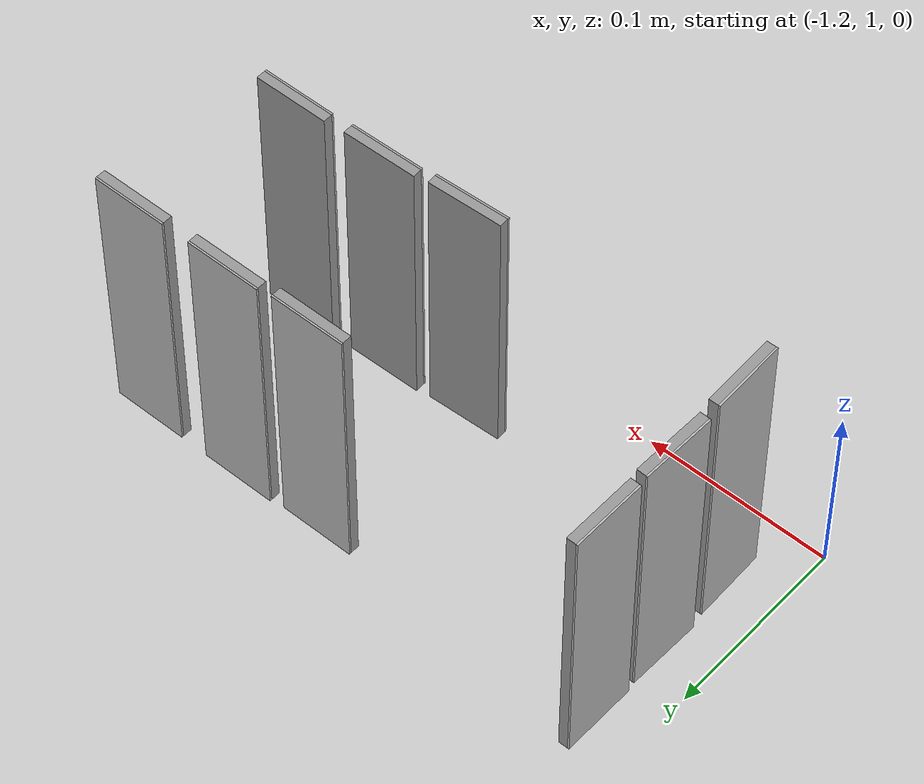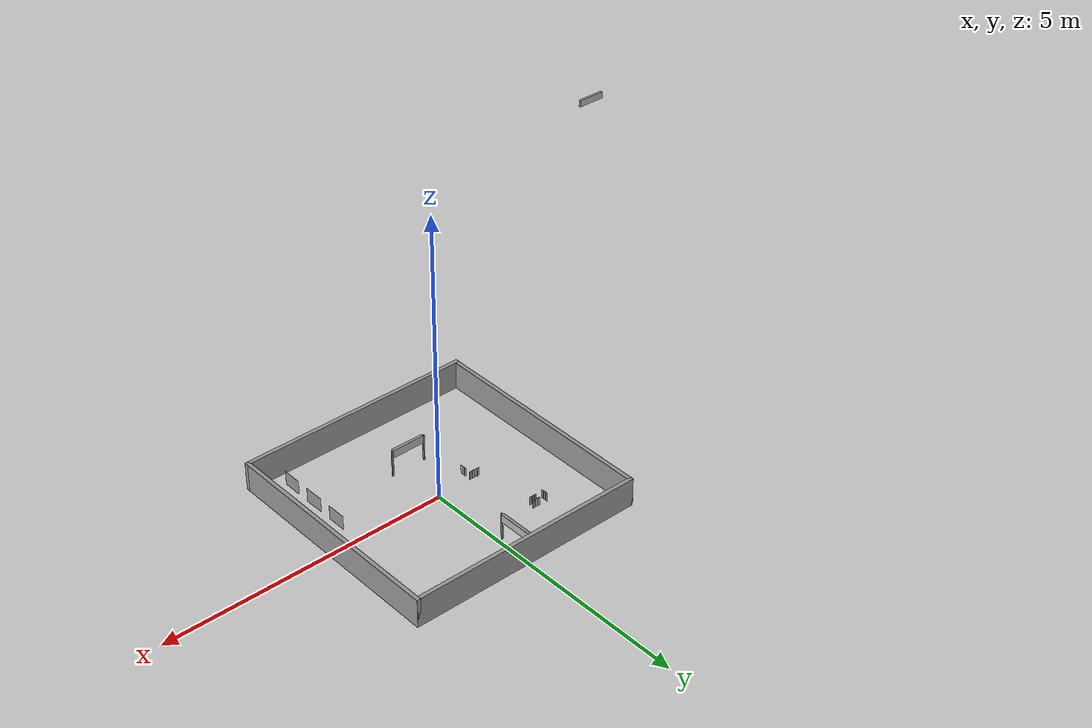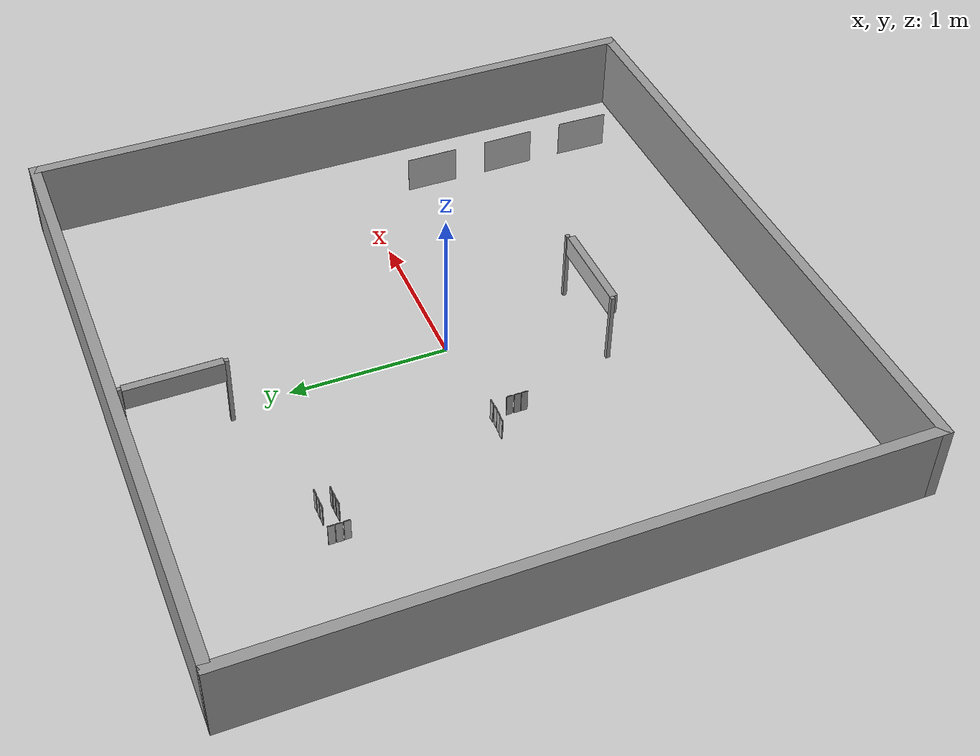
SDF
<sdf version="1.7">
 <world name="default">
  <light name="sun" type="directional">
   <pose>0 0 10 0 -0 0</pose>
   <diffuse>0.8 0.8 0.8 1</diffuse>
   <specular>0.2 0.2 0.2 1</specular>
   <attenuation>
    <range>1000</range>
    <constant>0.9</constant>
    <linear>0.01</linear>
    <quadratic>0.001</quadratic>
   </attenuation>
   <direction>-0.5 0.1 -0.9</direction>
   <spot><inner_angle>0</inner_angle><outer_angle>0</outer_angle><falloff>0</falloff></spot>
  </light>
  <model name="ground_plane">
   <static>1</static>
   <link name="link">
    <collision name="collision">
     <geometry><plane><normal>0 0 1</normal><size>100 100</size></plane></geometry>
     <surface>
      <contact><collide_bitmask>65535</collide_bitmask></contact>
      <friction><ode><mu>100</mu><mu2>50</mu2></ode></friction>
     </surface>
    </collision>
    <visual name="visual">
     <cast_shadows>0</cast_shadows>
     <geometry><plane><normal>0 0 1</normal><size>4.2 4.2</size></plane></geometry>
     <material><script><uri>file:///home/ros1/桌面/2/png1.material</uri><name>png1</name></script></material>
    </visual>
   </link>
  </model>
  <gravity>0 0 -9.8</gravity>
  <magnetic_field>6e-06 2.3e-05 -4.2e-05</magnetic_field>
  <atmosphere type="adiabatic"/>
  <physics type="ode">
   <max_step_size>0.001</max_step_size>
   <real_time_factor>1</real_time_factor>
   <real_time_update_rate>1000</real_time_update_rate>
  </physics>
  <scene><ambient>0.4 0.4 0.4 1</ambient><background>0.7 0.7 0.7 1</background><shadows>1</shadows></scene>
  <spherical_coordinates>
   <surface_model>EARTH_WGS84</surface_model>
   <latitude_deg>0</latitude_deg>
   <longitude_deg>0</longitude_deg>
   <elevation>0</elevation>
   <heading_deg>0</heading_deg>
  </spherical_coordinates>
  <model name="car1">
   <link name="link_0">
    <inertial>
     <mass>1</mass>
     <inertia>
      <ixx>0.166667</ixx>
      <ixy>0</ixy>
      <ixz>0</ixz>
      <iyy>0.166667</iyy>
      <iyz>0</iyz>
      <izz>0.166667</izz>
     </inertia>
    </inertial>
    <pose>0 -0.000125 -0 0 -0 0</pose>
    <visual name="visual">
     <geometry><box><size>0.345 0.0004 0.25</size></box></geometry>
     <material>
      <lighting>1</lighting>
      <script><uri>file://media/materials/scripts/gazebo.material</uri><name>Gazebo/Grey</name></script>
      <shader type="pixel"><normal_map>__default__</normal_map></shader>
      <ambient>0.3 0.3 0.3 1</ambient>
      <diffuse>0.7 0.7 0.7 1</diffuse>
      <specular>0.01 0.01 0.01 1</specular>
      <emissive>0 0 0 1</emissive>
     </material>
    </visual>
    <collision name="collision">
     <geometry><box><size>0.345 0.0004 0.25</size></box></geometry>
     <surface>
      <friction>
       <ode><mu>1</mu><mu2>1</mu2><fdir1>0 0 0</fdir1><slip1>0</slip1><slip2>0</slip2></ode>
       <torsional>
        <coefficient>1</coefficient>
        <patch_radius>0</patch_radius>
        <surface_radius>0</surface_radius>
        <use_patch_radius>1</use_patch_radius>
        <ode><slip>0</slip></ode>
       </torsional>
      </friction>
      <bounce><restitution_coefficient>0</restitution_coefficient><threshold>1e+06</threshold></bounce>
      <contact>
       <collide_without_contact>0</collide_without_contact>
       <collide_without_contact_bitmask>1</collide_without_contact_bitmask>
       <collide_bitmask>1</collide_bitmask>
       <ode>
        <soft_cfm>0</soft_cfm>
        <soft_erp>0.2</soft_erp>
        <kp>1e+13</kp>
        <kd>1</kd>
        <max_vel>0.01</max_vel>
        <min_depth>0</min_depth>
       </ode>
       <bullet>
        <split_impulse>1</split_impulse>
        <split_impulse_penetration_threshold>-0.01</split_impulse_penetration_threshold>
        <soft_cfm>0</soft_cfm>
        <soft_erp>0.2</soft_erp>
        <kp>1e+13</kp>
        <kd>1</kd>
       </bullet>
      </contact>
     </surface>
    </collision>
   </link>
   <link name="link_1">
    <inertial>
     <mass>1</mass>
     <inertia>
      <ixx>0.166667</ixx>
      <ixy>0</ixy>
      <ixz>0</ixz>
      <iyy>0.166667</iyy>
      <iyz>0</iyz>
      <izz>0.166667</izz>
     </inertia>
    </inertial>
    <pose>0 0.000125 -0 0 -0 0</pose>
    <visual name="visual">
     <geometry><box><size>0.345 0.0001 0.25</size></box></geometry>
     <material>
      <lighting>1</lighting>
      <script><uri>file:///home/ros1/model_editor_models/car1/car1.material</uri><name>car1</name></script>
     </material>
    </visual>
    <collision name="collision">
     <geometry><box><size>0.345 0.0001 0.25</size></box></geometry>
     <surface>
      <friction>
       <ode><mu>1</mu><mu2>1</mu2><fdir1>0 0 0</fdir1><slip1>0</slip1><slip2>0</slip2></ode>
       <torsional>
        <coefficient>1</coefficient>
        <patch_radius>0</patch_radius>
        <surface_radius>0</surface_radius>
        <use_patch_radius>1</use_patch_radius>
        <ode><slip>0</slip></ode>
       </torsional>
      </friction>
      <bounce><restitution_coefficient>0</restitution_coefficient><threshold>1e+06</threshold></bounce>
      <contact>
       <collide_without_contact>0</collide_without_contact>
       <collide_without_contact_bitmask>1</collide_without_contact_bitmask>
       <collide_bitmask>1</collide_bitmask>
       <ode>
        <soft_cfm>0</soft_cfm>
        <soft_erp>0.2</soft_erp>
        <kp>1e+13</kp>
        <kd>1</kd>
        <max_vel>0.01</max_vel>
        <min_depth>0</min_depth>
       </ode>
       <bullet>
        <split_impulse>1</split_impulse>
        <split_impulse_penetration_threshold>-0.01</split_impulse_penetration_threshold>
        <soft_cfm>0</soft_cfm>
        <soft_erp>0.2</soft_erp>
        <kp>1e+13</kp>
        <kd>1</kd>
       </bullet>
      </contact>
     </surface>
    </collision>
   </link>
   <static>0</static>
   <pose>1.56151 -1.63759 0.125 1e-06 -0 1.55632</pose>
  </model>
  <model name="car1_0">
   <link name="link_0">
    <inertial>
     <mass>1</mass>
     <inertia>
      <ixx>0.166667</ixx>
      <ixy>0</ixy>
      <ixz>0</ixz>
      <iyy>0.166667</iyy>
      <iyz>0</iyz>
      <izz>0.166667</izz>
     </inertia>
    </inertial>
    <pose>0 -0.000125 -0 0 -0 0</pose>
    <visual name="visual">
     <geometry><box><size>0.345 0.0004 0.25</size></box></geometry>
     <material>
      <lighting>1</lighting>
      <script><uri>file://media/materials/scripts/gazebo.material</uri><name>Gazebo/Grey</name></script>
      <shader type="pixel"><normal_map>__default__</normal_map></shader>
      <ambient>0.3 0.3 0.3 1</ambient>
      <diffuse>0.7 0.7 0.7 1</diffuse>
      <specular>0.01 0.01 0.01 1</specular>
      <emissive>0 0 0 1</emissive>
     </material>
    </visual>
    <collision name="collision">
     <geometry><box><size>0.345 0.0004 0.25</size></box></geometry>
     <surface>
      <friction>
       <ode><mu>1</mu><mu2>1</mu2><fdir1>0 0 0</fdir1><slip1>0</slip1><slip2>0</slip2></ode>
       <torsional>
        <coefficient>1</coefficient>
        <patch_radius>0</patch_radius>
        <surface_radius>0</surface_radius>
        <use_patch_radius>1</use_patch_radius>
        <ode><slip>0</slip></ode>
       </torsional>
      </friction>
      <bounce><restitution_coefficient>0</restitution_coefficient><threshold>1e+06</threshold></bounce>
      <contact>
       <collide_without_contact>0</collide_without_contact>
       <collide_without_contact_bitmask>1</collide_without_contact_bitmask>
       <collide_bitmask>1</collide_bitmask>
       <ode>
        <soft_cfm>0</soft_cfm>
        <soft_erp>0.2</soft_erp>
        <kp>1e+13</kp>
        <kd>1</kd>
        <max_vel>0.01</max_vel>
        <min_depth>0</min_depth>
       </ode>
       <bullet>
        <split_impulse>1</split_impulse>
        <split_impulse_penetration_threshold>-0.01</split_impulse_penetration_threshold>
        <soft_cfm>0</soft_cfm>
        <soft_erp>0.2</soft_erp>
        <kp>1e+13</kp>
        <kd>1</kd>
       </bullet>
      </contact>
     </surface>
    </collision>
   </link>
   <link name="link_1">
    <inertial>
     <mass>1</mass>
     <inertia>
      <ixx>0.166667</ixx>
      <ixy>0</ixy>
      <ixz>0</ixz>
      <iyy>0.166667</iyy>
      <iyz>0</iyz>
      <izz>0.166667</izz>
     </inertia>
    </inertial>
    <pose>0 0.000125 -0 0 -0 0</pose>
    <visual name="visual">
     <geometry><box><size>0.345 0.0001 0.25</size></box></geometry>
     <material>
      <lighting>1</lighting>
      <script><uri>file:///home/ros1/model_editor_models/car2/car2.material</uri><name>car2</name></script>
     </material>
    </visual>
    <collision name="collision">
     <geometry><box><size>0.345 0.0001 0.25</size></box></geometry>
     <surface>
      <friction>
       <ode><mu>1</mu><mu2>1</mu2><fdir1>0 0 0</fdir1><slip1>0</slip1><slip2>0</slip2></ode>
       <torsional>
        <coefficient>1</coefficient>
        <patch_radius>0</patch_radius>
        <surface_radius>0</surface_radius>
        <use_patch_radius>1</use_patch_radius>
        <ode><slip>0</slip></ode>
       </torsional>
      </friction>
      <bounce><restitution_coefficient>0</restitution_coefficient><threshold>1e+06</threshold></bounce>
      <contact>
       <collide_without_contact>0</collide_without_contact>
       <collide_without_contact_bitmask>1</collide_without_contact_bitmask>
       <collide_bitmask>1</collide_bitmask>
       <ode>
        <soft_cfm>0</soft_cfm>
        <soft_erp>0.2</soft_erp>
        <kp>1e+13</kp>
        <kd>1</kd>
        <max_vel>0.01</max_vel>
        <min_depth>0</min_depth>
       </ode>
       <bullet>
        <split_impulse>1</split_impulse>
        <split_impulse_penetration_threshold>-0.01</split_impulse_penetration_threshold>
        <soft_cfm>0</soft_cfm>
        <soft_erp>0.2</soft_erp>
        <kp>1e+13</kp>
        <kd>1</kd>
       </bullet>
      </contact>
     </surface>
    </collision>
   </link>
   <static>0</static>
   <pose>1.56242 -1.07814 0.125 0 -0 1.5863</pose>
  </model>
  <model name="car1_1">
   <link name="link_0">
    <inertial>
     <mass>1</mass>
     <inertia>
      <ixx>0.166667</ixx>
      <ixy>0</ixy>
      <ixz>0</ixz>
      <iyy>0.166667</iyy>
      <iyz>0</iyz>
      <izz>0.166667</izz>
     </inertia>
    </inertial>
    <pose>0 -0.000125 -0 0 -0 0</pose>
    <visual name="visual">
     <geometry><box><size>0.345 0.0004 0.25</size></box></geometry>
     <material>
      <lighting>1</lighting>
      <script><uri>file://media/materials/scripts/gazebo.material</uri><name>Gazebo/Grey</name></script>
      <shader type="pixel"><normal_map>__default__</normal_map></shader>
      <ambient>0.3 0.3 0.3 1</ambient>
      <diffuse>0.7 0.7 0.7 1</diffuse>
      <specular>0.01 0.01 0.01 1</specular>
      <emissive>0 0 0 1</emissive>
     </material>
    </visual>
    <collision name="collision">
     <geometry><box><size>0.345 0.0004 0.25</size></box></geometry>
     <surface>
      <friction>
       <ode><mu>1</mu><mu2>1</mu2><fdir1>0 0 0</fdir1><slip1>0</slip1><slip2>0</slip2></ode>
       <torsional>
        <coefficient>1</coefficient>
        <patch_radius>0</patch_radius>
        <surface_radius>0</surface_radius>
        <use_patch_radius>1</use_patch_radius>
        <ode><slip>0</slip></ode>
       </torsional>
      </friction>
      <bounce><restitution_coefficient>0</restitution_coefficient><threshold>1e+06</threshold></bounce>
      <contact>
       <collide_without_contact>0</collide_without_contact>
       <collide_without_contact_bitmask>1</collide_without_contact_bitmask>
       <collide_bitmask>1</collide_bitmask>
       <ode>
        <soft_cfm>0</soft_cfm>
        <soft_erp>0.2</soft_erp>
        <kp>1e+13</kp>
        <kd>1</kd>
        <max_vel>0.01</max_vel>
        <min_depth>0</min_depth>
       </ode>
       <bullet>
        <split_impulse>1</split_impulse>
        <split_impulse_penetration_threshold>-0.01</split_impulse_penetration_threshold>
        <soft_cfm>0</soft_cfm>
        <soft_erp>0.2</soft_erp>
        <kp>1e+13</kp>
        <kd>1</kd>
       </bullet>
      </contact>
     </surface>
    </collision>
   </link>
   <link name="link_1">
    <inertial>
     <mass>1</mass>
     <inertia>
      <ixx>0.166667</ixx>
      <ixy>0</ixy>
      <ixz>0</ixz>
      <iyy>0.166667</iyy>
      <iyz>0</iyz>
      <izz>0.166667</izz>
     </inertia>
    </inertial>
    <pose>0 0.000125 -0 0 -0 0</pose>
    <visual name="visual">
     <geometry><box><size>0.345 0.0001 0.25</size></box></geometry>
     <material>
      <lighting>1</lighting>
      <script><uri>file:///home/ros1/model_editor_models/car3/car3.material</uri><name>car3</name></script>
     </material>
    </visual>
    <collision name="collision">
     <geometry><box><size>0.345 0.0001 0.25</size></box></geometry>
     <surface>
      <friction>
       <ode><mu>1</mu><mu2>1</mu2><fdir1>0 0 0</fdir1><slip1>0</slip1><slip2>0</slip2></ode>
       <torsional>
        <coefficient>1</coefficient>
        <patch_radius>0</patch_radius>
        <surface_radius>0</surface_radius>
        <use_patch_radius>1</use_patch_radius>
        <ode><slip>0</slip></ode>
       </torsional>
      </friction>
      <bounce><restitution_coefficient>0</restitution_coefficient><threshold>1e+06</threshold></bounce>
      <contact>
       <collide_without_contact>0</collide_without_contact>
       <collide_without_contact_bitmask>1</collide_without_contact_bitmask>
       <collide_bitmask>1</collide_bitmask>
       <ode>
        <soft_cfm>0</soft_cfm>
        <soft_erp>0.2</soft_erp>
        <kp>1e+13</kp>
        <kd>1</kd>
        <max_vel>0.01</max_vel>
        <min_depth>0</min_depth>
       </ode>
       <bullet>
        <split_impulse>1</split_impulse>
        <split_impulse_penetration_threshold>-0.01</split_impulse_penetration_threshold>
        <soft_cfm>0</soft_cfm>
        <soft_erp>0.2</soft_erp>
        <kp>1e+13</kp>
        <kd>1</kd>
       </bullet>
      </contact>
     </surface>
    </collision>
   </link>
   <static>0</static>
   <pose>1.56249 -0.521605 0.124999 0 4e-06 1.5704</pose>
  </model>
  <model name="F1">
   <link name="link_0">
    <inertial>
     <mass>1</mass>
     <inertia>
      <ixx>0.166667</ixx>
      <ixy>0</ixy>
      <ixz>0</ixz>
      <iyy>0.166667</iyy>
      <iyz>0</iyz>
      <izz>0.166667</izz>
     </inertia>
    </inertial>
    <pose>0 -0.0015 -0 0 -0 0</pose>
    <visual name="visual">
     <geometry><box><size>0.04 0.005 0.15</size></box></geometry>
     <material>
      <lighting>1</lighting>
      <script><uri>file://media/materials/scripts/gazebo.material</uri><name>Gazebo/Grey</name></script>
      <shader type="pixel"><normal_map>__default__</normal_map></shader>
      <ambient>0.3 0.3 0.3 1</ambient>
      <diffuse>0.7 0.7 0.7 1</diffuse>
      <specular>0.01 0.01 0.01 1</specular>
      <emissive>0 0 0 1</emissive>
     </material>
    </visual>
    <collision name="collision">
     <geometry><box><size>0.04 0.005 0.15</size></box></geometry>
     <surface>
      <friction>
       <ode><mu>1</mu><mu2>1</mu2><fdir1>0 0 0</fdir1><slip1>0</slip1><slip2>0</slip2></ode>
       <torsional>
        <coefficient>1</coefficient>
        <patch_radius>0</patch_radius>
        <surface_radius>0</surface_radius>
        <use_patch_radius>1</use_patch_radius>
        <ode><slip>0</slip></ode>
       </torsional>
      </friction>
      <bounce><restitution_coefficient>0</restitution_coefficient><threshold>1e+06</threshold></bounce>
      <contact>
       <collide_without_contact>0</collide_without_contact>
       <collide_without_contact_bitmask>1</collide_without_contact_bitmask>
       <collide_bitmask>1</collide_bitmask>
       <ode>
        <soft_cfm>0</soft_cfm>
        <soft_erp>0.2</soft_erp>
        <kp>1e+13</kp>
        <kd>1</kd>
        <max_vel>0.01</max_vel>
        <min_depth>0</min_depth>
       </ode>
       <bullet>
        <split_impulse>1</split_impulse>
        <split_impulse_penetration_threshold>-0.01</split_impulse_penetration_threshold>
        <soft_cfm>0</soft_cfm>
        <soft_erp>0.2</soft_erp>
        <kp>1e+13</kp>
        <kd>1</kd>
       </bullet>
      </contact>
     </surface>
    </collision>
   </link>
   <link name="link_4">
    <inertial>
     <mass>1</mass>
     <inertia>
      <ixx>0.166667</ixx>
      <ixy>0</ixy>
      <ixz>0</ixz>
      <iyy>0.166667</iyy>
      <iyz>0</iyz>
      <izz>0.166667</izz>
     </inertia>
    </inertial>
    <pose>0 0.0015 -0 0 -0 0</pose>
    <visual name="visual">
     <geometry><box><size>0.04 0.001 0.15</size></box></geometry>
     <material>
      <script><uri>file:///home/ros1/model_editor_models/F1/F1.material</uri><name>F1</name></script>
     </material>
    </visual>
    <collision name="collision">
     <geometry><box><size>0.04 0.001 0.15</size></box></geometry>
     <surface>
      <friction>
       <ode><mu>1</mu><mu2>1</mu2><fdir1>0 0 0</fdir1><slip1>0</slip1><slip2>0</slip2></ode>
       <torsional>
        <coefficient>1</coefficient>
        <patch_radius>0</patch_radius>
        <surface_radius>0</surface_radius>
        <use_patch_radius>1</use_patch_radius>
        <ode><slip>0</slip></ode>
       </torsional>
      </friction>
      <bounce><restitution_coefficient>0</restitution_coefficient><threshold>1e+06</threshold></bounce>
      <contact>
       <collide_without_contact>0</collide_without_contact>
       <collide_without_contact_bitmask>1</collide_without_contact_bitmask>
       <collide_bitmask>1</collide_bitmask>
       <ode>
        <soft_cfm>0</soft_cfm>
        <soft_erp>0.2</soft_erp>
        <kp>1e+13</kp>
        <kd>1</kd>
        <max_vel>0.01</max_vel>
        <min_depth>0</min_depth>
       </ode>
       <bullet>
        <split_impulse>1</split_impulse>
        <split_impulse_penetration_threshold>-0.01</split_impulse_penetration_threshold>
        <soft_cfm>0</soft_cfm>
        <soft_erp>0.2</soft_erp>
        <kp>1e+13</kp>
        <kd>1</kd>
       </bullet>
      </contact>
     </surface>
    </collision>
   </link>
   <static>0</static>
   <pose>-0.916044 1.13743 0.075 -1.4e-05 -3e-06 -5.4e-05</pose>
  </model>
  <model name="man-4">
   <link name="link_0">
    <inertial>
     <mass>1</mass>
     <inertia>
      <ixx>0.166667</ixx>
      <ixy>0</ixy>
      <ixz>0</ixz>
      <iyy>0.166667</iyy>
      <iyz>0</iyz>
      <izz>0.166667</izz>
     </inertia>
    </inertial>
    <pose>0 -0.0015 -0 0 -0 0</pose>
    <visual name="visual">
     <geometry><box><size>0.04 0.005 0.15</size></box></geometry>
     <material>
      <lighting>1</lighting>
      <script><uri>file://media/materials/scripts/gazebo.material</uri><name>Gazebo/Grey</name></script>
      <shader type="pixel"><normal_map>__default__</normal_map></shader>
      <ambient>0.3 0.3 0.3 1</ambient>
      <diffuse>0.7 0.7 0.7 1</diffuse>
      <specular>0.01 0.01 0.01 1</specular>
      <emissive>0 0 0 1</emissive>
     </material>
    </visual>
    <collision name="collision">
     <geometry><box><size>0.04 0.005 0.15</size></box></geometry>
     <surface>
      <friction>
       <ode><mu>1</mu><mu2>1</mu2><fdir1>0 0 0</fdir1><slip1>0</slip1><slip2>0</slip2></ode>
       <torsional>
        <coefficient>1</coefficient>
        <patch_radius>0</patch_radius>
        <surface_radius>0</surface_radius>
        <use_patch_radius>1</use_patch_radius>
        <ode><slip>0</slip></ode>
       </torsional>
      </friction>
      <bounce><restitution_coefficient>0</restitution_coefficient><threshold>1e+06</threshold></bounce>
      <contact>
       <collide_without_contact>0</collide_without_contact>
       <collide_without_contact_bitmask>1</collide_without_contact_bitmask>
       <collide_bitmask>1</collide_bitmask>
       <ode>
        <soft_cfm>0</soft_cfm>
        <soft_erp>0.2</soft_erp>
        <kp>1e+13</kp>
        <kd>1</kd>
        <max_vel>0.01</max_vel>
        <min_depth>0</min_depth>
       </ode>
       <bullet>
        <split_impulse>1</split_impulse>
        <split_impulse_penetration_threshold>-0.01</split_impulse_penetration_threshold>
        <soft_cfm>0</soft_cfm>
        <soft_erp>0.2</soft_erp>
        <kp>1e+13</kp>
        <kd>1</kd>
       </bullet>
      </contact>
     </surface>
    </collision>
   </link>
   <link name="link_4">
    <inertial>
     <mass>1</mass>
     <inertia>
      <ixx>0.166667</ixx>
      <ixy>0</ixy>
      <ixz>0</ixz>
      <iyy>0.166667</iyy>
      <iyz>0</iyz>
      <izz>0.166667</izz>
     </inertia>
    </inertial>
    <pose>0 0.0015 -0 0 -0 0</pose>
    <visual name="visual">
     <geometry><box><size>0.04 0.001 0.15</size></box></geometry>
     <material>
      <script><uri>file:///home/ros1/model_editor_models/man-4/man_4.material</uri><name>man_4</name></script>
     </material>
    </visual>
    <collision name="collision">
     <geometry><box><size>0.04 0.001 0.15</size></box></geometry>
     <surface>
      <friction>
       <ode><mu>1</mu><mu2>1</mu2><fdir1>0 0 0</fdir1><slip1>0</slip1><slip2>0</slip2></ode>
       <torsional>
        <coefficient>1</coefficient>
        <patch_radius>0</patch_radius>
        <surface_radius>0</surface_radius>
        <use_patch_radius>1</use_patch_radius>
        <ode><slip>0</slip></ode>
       </torsional>
      </friction>
      <bounce><restitution_coefficient>0</restitution_coefficient><threshold>1e+06</threshold></bounce>
      <contact>
       <collide_without_contact>0</collide_without_contact>
       <collide_without_contact_bitmask>1</collide_without_contact_bitmask>
       <collide_bitmask>1</collide_bitmask>
       <ode>
        <soft_cfm>0</soft_cfm>
        <soft_erp>0.2</soft_erp>
        <kp>1e+13</kp>
        <kd>1</kd>
        <max_vel>0.01</max_vel>
        <min_depth>0</min_depth>
       </ode>
       <bullet>
        <split_impulse>1</split_impulse>
        <split_impulse_penetration_threshold>-0.01</split_impulse_penetration_threshold>
        <soft_cfm>0</soft_cfm>
        <soft_erp>0.2</soft_erp>
        <kp>1e+13</kp>
        <kd>1</kd>
       </bullet>
      </contact>
     </surface>
    </collision>
   </link>
   <static>0</static>
   <pose>-1.17659 1.08772 0.075 -1.9e-05 3e-06 1.54319</pose>
  </model>
  <model name="man-5">
   <link name="link_0">
    <inertial>
     <mass>1</mass>
     <inertia>
      <ixx>0.166667</ixx>
      <ixy>0</ixy>
      <ixz>0</ixz>
      <iyy>0.166667</iyy>
      <iyz>0</iyz>
      <izz>0.166667</izz>
     </inertia>
    </inertial>
    <pose>0 -0.0015 -0 0 -0 0</pose>
    <visual name="visual">
     <geometry><box><size>0.04 0.005 0.15</size></box></geometry>
     <material>
      <lighting>1</lighting>
      <script><uri>file://media/materials/scripts/gazebo.material</uri><name>Gazebo/Grey</name></script>
      <shader type="pixel"><normal_map>__default__</normal_map></shader>
      <ambient>0.3 0.3 0.3 1</ambient>
      <diffuse>0.7 0.7 0.7 1</diffuse>
      <specular>0.01 0.01 0.01 1</specular>
      <emissive>0 0 0 1</emissive>
     </material>
    </visual>
    <collision name="collision">
     <geometry><box><size>0.04 0.005 0.15</size></box></geometry>
     <surface>
      <friction>
       <ode><mu>1</mu><mu2>1</mu2><fdir1>0 0 0</fdir1><slip1>0</slip1><slip2>0</slip2></ode>
       <torsional>
        <coefficient>1</coefficient>
        <patch_radius>0</patch_radius>
        <surface_radius>0</surface_radius>
        <use_patch_radius>1</use_patch_radius>
        <ode><slip>0</slip></ode>
       </torsional>
      </friction>
      <bounce><restitution_coefficient>0</restitution_coefficient><threshold>1e+06</threshold></bounce>
      <contact>
       <collide_without_contact>0</collide_without_contact>
       <collide_without_contact_bitmask>1</collide_without_contact_bitmask>
       <collide_bitmask>1</collide_bitmask>
       <ode>
        <soft_cfm>0</soft_cfm>
        <soft_erp>0.2</soft_erp>
        <kp>1e+13</kp>
        <kd>1</kd>
        <max_vel>0.01</max_vel>
        <min_depth>0</min_depth>
       </ode>
       <bullet>
        <split_impulse>1</split_impulse>
        <split_impulse_penetration_threshold>-0.01</split_impulse_penetration_threshold>
        <soft_cfm>0</soft_cfm>
        <soft_erp>0.2</soft_erp>
        <kp>1e+13</kp>
        <kd>1</kd>
       </bullet>
      </contact>
     </surface>
    </collision>
   </link>
   <link name="link_4">
    <inertial>
     <mass>1</mass>
     <inertia>
      <ixx>0.166667</ixx>
      <ixy>0</ixy>
      <ixz>0</ixz>
      <iyy>0.166667</iyy>
      <iyz>0</iyz>
      <izz>0.166667</izz>
     </inertia>
    </inertial>
    <pose>0 0.0015 -0 0 -0 0</pose>
    <visual name="visual">
     <geometry><box><size>0.04 0.001 0.15</size></box></geometry>
     <material>
      <script><uri>file:///home/ros1/model_editor_models/man-5/man_5.material</uri><name>man_5</name></script>
     </material>
    </visual>
    <collision name="collision">
     <geometry><box><size>0.04 0.001 0.15</size></box></geometry>
     <surface>
      <friction>
       <ode><mu>1</mu><mu2>1</mu2><fdir1>0 0 0</fdir1><slip1>0</slip1><slip2>0</slip2></ode>
       <torsional>
        <coefficient>1</coefficient>
        <patch_radius>0</patch_radius>
        <surface_radius>0</surface_radius>
        <use_patch_radius>1</use_patch_radius>
        <ode><slip>0</slip></ode>
       </torsional>
      </friction>
      <bounce><restitution_coefficient>0</restitution_coefficient><threshold>1e+06</threshold></bounce>
      <contact>
       <collide_without_contact>0</collide_without_contact>
       <collide_without_contact_bitmask>1</collide_without_contact_bitmask>
       <collide_bitmask>1</collide_bitmask>
       <ode>
        <soft_cfm>0</soft_cfm>
        <soft_erp>0.2</soft_erp>
        <kp>1e+13</kp>
        <kd>1</kd>
        <max_vel>0.01</max_vel>
        <min_depth>0</min_depth>
       </ode>
       <bullet>
        <split_impulse>1</split_impulse>
        <split_impulse_penetration_threshold>-0.01</split_impulse_penetration_threshold>
        <soft_cfm>0</soft_cfm>
        <soft_erp>0.2</soft_erp>
        <kp>1e+13</kp>
        <kd>1</kd>
       </bullet>
      </contact>
     </surface>
    </collision>
   </link>
   <static>0</static>
   <pose>-1.17679 1.13259 0.075001 -1.6e-05 -3.5e-05 1.56191</pose>
  </model>
  <model name="man-6">
   <link name="link_0">
    <inertial>
     <mass>1</mass>
     <inertia>
      <ixx>0.166667</ixx>
      <ixy>0</ixy>
      <ixz>0</ixz>
      <iyy>0.166667</iyy>
      <iyz>0</iyz>
      <izz>0.166667</izz>
     </inertia>
    </inertial>
    <pose>0 -0.0015 -0 0 -0 0</pose>
    <visual name="visual">
     <geometry><box><size>0.04 0.005 0.15</size></box></geometry>
     <material>
      <lighting>1</lighting>
      <script><uri>file://media/materials/scripts/gazebo.material</uri><name>Gazebo/Grey</name></script>
      <shader type="pixel"><normal_map>__default__</normal_map></shader>
      <ambient>0.3 0.3 0.3 1</ambient>
      <diffuse>0.7 0.7 0.7 1</diffuse>
      <specular>0.01 0.01 0.01 1</specular>
      <emissive>0 0 0 1</emissive>
     </material>
    </visual>
    <collision name="collision">
     <geometry><box><size>0.04 0.005 0.15</size></box></geometry>
     <surface>
      <friction>
       <ode><mu>1</mu><mu2>1</mu2><fdir1>0 0 0</fdir1><slip1>0</slip1><slip2>0</slip2></ode>
       <torsional>
        <coefficient>1</coefficient>
        <patch_radius>0</patch_radius>
        <surface_radius>0</surface_radius>
        <use_patch_radius>1</use_patch_radius>
        <ode><slip>0</slip></ode>
       </torsional>
      </friction>
      <bounce><restitution_coefficient>0</restitution_coefficient><threshold>1e+06</threshold></bounce>
      <contact>
       <collide_without_contact>0</collide_without_contact>
       <collide_without_contact_bitmask>1</collide_without_contact_bitmask>
       <collide_bitmask>1</collide_bitmask>
       <ode>
        <soft_cfm>0</soft_cfm>
        <soft_erp>0.2</soft_erp>
        <kp>1e+13</kp>
        <kd>1</kd>
        <max_vel>0.01</max_vel>
        <min_depth>0</min_depth>
       </ode>
       <bullet>
        <split_impulse>1</split_impulse>
        <split_impulse_penetration_threshold>-0.01</split_impulse_penetration_threshold>
        <soft_cfm>0</soft_cfm>
        <soft_erp>0.2</soft_erp>
        <kp>1e+13</kp>
        <kd>1</kd>
       </bullet>
      </contact>
     </surface>
    </collision>
   </link>
   <link name="link_4">
    <inertial>
     <mass>1</mass>
     <inertia>
      <ixx>0.166667</ixx>
      <ixy>0</ixy>
      <ixz>0</ixz>
      <iyy>0.166667</iyy>
      <iyz>0</iyz>
      <izz>0.166667</izz>
     </inertia>
    </inertial>
    <pose>0 0.0015 -0 0 -0 0</pose>
    <visual name="visual">
     <geometry><box><size>0.04 0.001 0.15</size></box></geometry>
     <material>
      <script><uri>file:///home/ros1/model_editor_models/man-6/man_6.material</uri><name>man_6</name></script>
     </material>
    </visual>
    <collision name="collision">
     <geometry><box><size>0.04 0.001 0.15</size></box></geometry>
     <surface>
      <friction>
       <ode><mu>1</mu><mu2>1</mu2><fdir1>0 0 0</fdir1><slip1>0</slip1><slip2>0</slip2></ode>
       <torsional>
        <coefficient>1</coefficient>
        <patch_radius>0</patch_radius>
        <surface_radius>0</surface_radius>
        <use_patch_radius>1</use_patch_radius>
        <ode><slip>0</slip></ode>
       </torsional>
      </friction>
      <bounce><restitution_coefficient>0</restitution_coefficient><threshold>1e+06</threshold></bounce>
      <contact>
       <collide_without_contact>0</collide_without_contact>
       <collide_without_contact_bitmask>1</collide_without_contact_bitmask>
       <collide_bitmask>1</collide_bitmask>
       <ode>
        <soft_cfm>0</soft_cfm>
        <soft_erp>0.2</soft_erp>
        <kp>1e+13</kp>
        <kd>1</kd>
        <max_vel>0.01</max_vel>
        <min_depth>0</min_depth>
       </ode>
       <bullet>
        <split_impulse>1</split_impulse>
        <split_impulse_penetration_threshold>-0.01</split_impulse_penetration_threshold>
        <soft_cfm>0</soft_cfm>
        <soft_erp>0.2</soft_erp>
        <kp>1e+13</kp>
        <kd>1</kd>
       </bullet>
      </contact>
     </surface>
    </collision>
   </link>
   <static>0</static>
   <pose>-1.02578 1.04198 0.075 1.5e-05 -8e-06 -3.0988</pose>
  </model>
  <model name="man-7">
   <link name="link_0">
    <inertial>
     <mass>1</mass>
     <inertia>
      <ixx>0.166667</ixx>
      <ixy>0</ixy>
      <ixz>0</ixz>
      <iyy>0.166667</iyy>
      <iyz>0</iyz>
      <izz>0.166667</izz>
     </inertia>
    </inertial>
    <pose>0 -0.0015 -0 0 -0 0</pose>
    <visual name="visual">
     <geometry><box><size>0.04 0.005 0.15</size></box></geometry>
     <material>
      <lighting>1</lighting>
      <script><uri>file://media/materials/scripts/gazebo.material</uri><name>Gazebo/Grey</name></script>
      <shader type="pixel"><normal_map>__default__</normal_map></shader>
      <ambient>0.3 0.3 0.3 1</ambient>
      <diffuse>0.7 0.7 0.7 1</diffuse>
      <specular>0.01 0.01 0.01 1</specular>
      <emissive>0 0 0 1</emissive>
     </material>
    </visual>
    <collision name="collision">
     <geometry><box><size>0.04 0.005 0.15</size></box></geometry>
     <surface>
      <friction>
       <ode><mu>1</mu><mu2>1</mu2><fdir1>0 0 0</fdir1><slip1>0</slip1><slip2>0</slip2></ode>
       <torsional>
        <coefficient>1</coefficient>
        <patch_radius>0</patch_radius>
        <surface_radius>0</surface_radius>
        <use_patch_radius>1</use_patch_radius>
        <ode><slip>0</slip></ode>
       </torsional>
      </friction>
      <bounce><restitution_coefficient>0</restitution_coefficient><threshold>1e+06</threshold></bounce>
      <contact>
       <collide_without_contact>0</collide_without_contact>
       <collide_without_contact_bitmask>1</collide_without_contact_bitmask>
       <collide_bitmask>1</collide_bitmask>
       <ode>
        <soft_cfm>0</soft_cfm>
        <soft_erp>0.2</soft_erp>
        <kp>1e+13</kp>
        <kd>1</kd>
        <max_vel>0.01</max_vel>
        <min_depth>0</min_depth>
       </ode>
       <bullet>
        <split_impulse>1</split_impulse>
        <split_impulse_penetration_threshold>-0.01</split_impulse_penetration_threshold>
        <soft_cfm>0</soft_cfm>
        <soft_erp>0.2</soft_erp>
        <kp>1e+13</kp>
        <kd>1</kd>
       </bullet>
      </contact>
     </surface>
    </collision>
   </link>
   <link name="link_4">
    <inertial>
     <mass>1</mass>
     <inertia>
      <ixx>0.166667</ixx>
      <ixy>0</ixy>
      <ixz>0</ixz>
      <iyy>0.166667</iyy>
      <iyz>0</iyz>
      <izz>0.166667</izz>
     </inertia>
    </inertial>
    <pose>0 0.0015 -0 0 -0 0</pose>
    <visual name="visual">
     <geometry><box><size>0.04 0.001 0.15</size></box></geometry>
     <material>
      <script><uri>file:///home/ros1/model_editor_models/man-7/man_7.material</uri><name>man_7</name></script>
     </material>
    </visual>
    <collision name="collision">
     <geometry><box><size>0.04 0.001 0.15</size></box></geometry>
     <surface>
      <friction>
       <ode><mu>1</mu><mu2>1</mu2><fdir1>0 0 0</fdir1><slip1>0</slip1><slip2>0</slip2></ode>
       <torsional>
        <coefficient>1</coefficient>
        <patch_radius>0</patch_radius>
        <surface_radius>0</surface_radius>
        <use_patch_radius>1</use_patch_radius>
        <ode><slip>0</slip></ode>
       </torsional>
      </friction>
      <bounce><restitution_coefficient>0</restitution_coefficient><threshold>1e+06</threshold></bounce>
      <contact>
       <collide_without_contact>0</collide_without_contact>
       <collide_without_contact_bitmask>1</collide_without_contact_bitmask>
       <collide_bitmask>1</collide_bitmask>
       <ode>
        <soft_cfm>0</soft_cfm>
        <soft_erp>0.2</soft_erp>
        <kp>1e+13</kp>
        <kd>1</kd>
        <max_vel>0.01</max_vel>
        <min_depth>0</min_depth>
       </ode>
       <bullet>
        <split_impulse>1</split_impulse>
        <split_impulse_penetration_threshold>-0.01</split_impulse_penetration_threshold>
        <soft_cfm>0</soft_cfm>
        <soft_erp>0.2</soft_erp>
        <kp>1e+13</kp>
        <kd>1</kd>
       </bullet>
      </contact>
     </surface>
    </collision>
   </link>
   <static>0</static>
   <pose>-0.979134 1.04472 0.075 2e-06 1.6e-05 -3.12381</pose>
  </model>
  <model name="F2">
   <link name="link_0">
    <inertial>
     <mass>1</mass>
     <inertia>
      <ixx>0.166667</ixx>
      <ixy>0</ixy>
      <ixz>0</ixz>
      <iyy>0.166667</iyy>
      <iyz>0</iyz>
      <izz>0.166667</izz>
     </inertia>
    </inertial>
    <pose>0 -0.0015 -0 0 -0 0</pose>
    <visual name="visual">
     <geometry><box><size>0.04 0.005 0.15</size></box></geometry>
     <material>
      <lighting>1</lighting>
      <script><uri>file://media/materials/scripts/gazebo.material</uri><name>Gazebo/Grey</name></script>
      <shader type="pixel"><normal_map>__default__</normal_map></shader>
      <ambient>0.3 0.3 0.3 1</ambient>
      <diffuse>0.7 0.7 0.7 1</diffuse>
      <specular>0.01 0.01 0.01 1</specular>
      <emissive>0 0 0 1</emissive>
     </material>
    </visual>
    <collision name="collision">
     <geometry><box><size>0.04 0.005 0.15</size></box></geometry>
     <surface>
      <friction>
       <ode><mu>1</mu><mu2>1</mu2><fdir1>0 0 0</fdir1><slip1>0</slip1><slip2>0</slip2></ode>
       <torsional>
        <coefficient>1</coefficient>
        <patch_radius>0</patch_radius>
        <surface_radius>0</surface_radius>
        <use_patch_radius>1</use_patch_radius>
        <ode><slip>0</slip></ode>
       </torsional>
      </friction>
      <bounce><restitution_coefficient>0</restitution_coefficient><threshold>1e+06</threshold></bounce>
      <contact>
       <collide_without_contact>0</collide_without_contact>
       <collide_without_contact_bitmask>1</collide_without_contact_bitmask>
       <collide_bitmask>1</collide_bitmask>
       <ode>
        <soft_cfm>0</soft_cfm>
        <soft_erp>0.2</soft_erp>
        <kp>1e+13</kp>
        <kd>1</kd>
        <max_vel>0.01</max_vel>
        <min_depth>0</min_depth>
       </ode>
       <bullet>
        <split_impulse>1</split_impulse>
        <split_impulse_penetration_threshold>-0.01</split_impulse_penetration_threshold>
        <soft_cfm>0</soft_cfm>
        <soft_erp>0.2</soft_erp>
        <kp>1e+13</kp>
        <kd>1</kd>
       </bullet>
      </contact>
     </surface>
    </collision>
   </link>
   <link name="link_4">
    <inertial>
     <mass>1</mass>
     <inertia>
      <ixx>0.166667</ixx>
      <ixy>0</ixy>
      <ixz>0</ixz>
      <iyy>0.166667</iyy>
      <iyz>0</iyz>
      <izz>0.166667</izz>
     </inertia>
    </inertial>
    <pose>0 0.0015 -0 0 -0 0</pose>
    <visual name="visual">
     <geometry><box><size>0.04 0.001 0.15</size></box></geometry>
     <material>
      <script><uri>file:///home/ros1/model_editor_models/F2/F2.material</uri><name>F2</name></script>
     </material>
    </visual>
    <collision name="collision">
     <geometry><box><size>0.04 0.001 0.15</size></box></geometry>
     <surface>
      <friction>
       <ode><mu>1</mu><mu2>1</mu2><fdir1>0 0 0</fdir1><slip1>0</slip1><slip2>0</slip2></ode>
       <torsional>
        <coefficient>1</coefficient>
        <patch_radius>0</patch_radius>
        <surface_radius>0</surface_radius>
        <use_patch_radius>1</use_patch_radius>
        <ode><slip>0</slip></ode>
       </torsional>
      </friction>
      <bounce><restitution_coefficient>0</restitution_coefficient><threshold>1e+06</threshold></bounce>
      <contact>
       <collide_without_contact>0</collide_without_contact>
       <collide_without_contact_bitmask>1</collide_without_contact_bitmask>
       <collide_bitmask>1</collide_bitmask>
       <ode>
        <soft_cfm>0</soft_cfm>
        <soft_erp>0.2</soft_erp>
        <kp>1e+13</kp>
        <kd>1</kd>
        <max_vel>0.01</max_vel>
        <min_depth>0</min_depth>
       </ode>
       <bullet>
        <split_impulse>1</split_impulse>
        <split_impulse_penetration_threshold>-0.01</split_impulse_penetration_threshold>
        <soft_cfm>0</soft_cfm>
        <soft_erp>0.2</soft_erp>
        <kp>1e+13</kp>
        <kd>1</kd>
       </bullet>
      </contact>
     </surface>
    </collision>
   </link>
   <static>0</static>
   <pose>-0.928452 1.04611 0.075 -2e-06 2e-06 -3.14147</pose>
  </model>
  <model name="man-8">
   <link name="link_0">
    <inertial>
     <mass>1</mass>
     <inertia>
      <ixx>0.166667</ixx>
      <ixy>0</ixy>
      <ixz>0</ixz>
      <iyy>0.166667</iyy>
      <iyz>0</iyz>
      <izz>0.166667</izz>
     </inertia>
    </inertial>
    <pose>0 -0.0015 -0 0 -0 0</pose>
    <visual name="visual">
     <geometry><box><size>0.04 0.005 0.15</size></box></geometry>
     <material>
      <lighting>1</lighting>
      <script><uri>file://media/materials/scripts/gazebo.material</uri><name>Gazebo/Grey</name></script>
      <shader type="pixel"><normal_map>__default__</normal_map></shader>
      <ambient>0.3 0.3 0.3 1</ambient>
      <diffuse>0.7 0.7 0.7 1</diffuse>
      <specular>0.01 0.01 0.01 1</specular>
      <emissive>0 0 0 1</emissive>
     </material>
    </visual>
    <collision name="collision">
     <geometry><box><size>0.04 0.005 0.15</size></box></geometry>
     <surface>
      <friction>
       <ode><mu>1</mu><mu2>1</mu2><fdir1>0 0 0</fdir1><slip1>0</slip1><slip2>0</slip2></ode>
       <torsional>
        <coefficient>1</coefficient>
        <patch_radius>0</patch_radius>
        <surface_radius>0</surface_radius>
        <use_patch_radius>1</use_patch_radius>
        <ode><slip>0</slip></ode>
       </torsional>
      </friction>
      <bounce><restitution_coefficient>0</restitution_coefficient><threshold>1e+06</threshold></bounce>
      <contact>
       <collide_without_contact>0</collide_without_contact>
       <collide_without_contact_bitmask>1</collide_without_contact_bitmask>
       <collide_bitmask>1</collide_bitmask>
       <ode>
        <soft_cfm>0</soft_cfm>
        <soft_erp>0.2</soft_erp>
        <kp>1e+13</kp>
        <kd>1</kd>
        <max_vel>0.01</max_vel>
        <min_depth>0</min_depth>
       </ode>
       <bullet>
        <split_impulse>1</split_impulse>
        <split_impulse_penetration_threshold>-0.01</split_impulse_penetration_threshold>
        <soft_cfm>0</soft_cfm>
        <soft_erp>0.2</soft_erp>
        <kp>1e+13</kp>
        <kd>1</kd>
       </bullet>
      </contact>
     </surface>
    </collision>
   </link>
   <link name="link_4">
    <inertial>
     <mass>1</mass>
     <inertia>
      <ixx>0.166667</ixx>
      <ixy>0</ixy>
      <ixz>0</ixz>
      <iyy>0.166667</iyy>
      <iyz>0</iyz>
      <izz>0.166667</izz>
     </inertia>
    </inertial>
    <pose>0 0.0015 -0 0 -0 0</pose>
    <visual name="visual">
     <geometry><box><size>0.04 0.001 0.15</size></box></geometry>
     <material>
      <script><uri>file:///home/ros1/model_editor_models/man-8/man_8.material</uri><name>man_8</name></script>
     </material>
    </visual>
    <collision name="collision">
     <geometry><box><size>0.04 0.001 0.15</size></box></geometry>
     <surface>
      <friction>
       <ode><mu>1</mu><mu2>1</mu2><fdir1>0 0 0</fdir1><slip1>0</slip1><slip2>0</slip2></ode>
       <torsional>
        <coefficient>1</coefficient>
        <patch_radius>0</patch_radius>
        <surface_radius>0</surface_radius>
        <use_patch_radius>1</use_patch_radius>
        <ode><slip>0</slip></ode>
       </torsional>
      </friction>
      <bounce><restitution_coefficient>0</restitution_coefficient><threshold>1e+06</threshold></bounce>
      <contact>
       <collide_without_contact>0</collide_without_contact>
       <collide_without_contact_bitmask>1</collide_without_contact_bitmask>
       <collide_bitmask>1</collide_bitmask>
       <ode>
        <soft_cfm>0</soft_cfm>
        <soft_erp>0.2</soft_erp>
        <kp>1e+13</kp>
        <kd>1</kd>
        <max_vel>0.01</max_vel>
        <min_depth>0</min_depth>
       </ode>
       <bullet>
        <split_impulse>1</split_impulse>
        <split_impulse_penetration_threshold>-0.01</split_impulse_penetration_threshold>
        <soft_cfm>0</soft_cfm>
        <soft_erp>0.2</soft_erp>
        <kp>1e+13</kp>
        <kd>1</kd>
       </bullet>
      </contact>
     </surface>
    </collision>
   </link>
   <static>0</static>
   <pose>-0.7429 -0.02823 0.075 6e-06 -8e-06 0.000166</pose>
  </model>
  <model name="man-9">
   <link name="link_0">
    <inertial>
     <mass>1</mass>
     <inertia>
      <ixx>0.166667</ixx>
      <ixy>0</ixy>
      <ixz>0</ixz>
      <iyy>0.166667</iyy>
      <iyz>0</iyz>
      <izz>0.166667</izz>
     </inertia>
    </inertial>
    <pose>0 -0.0015 -0 0 -0 0</pose>
    <visual name="visual">
     <geometry><box><size>0.04 0.005 0.15</size></box></geometry>
     <material>
      <lighting>1</lighting>
      <script><uri>file://media/materials/scripts/gazebo.material</uri><name>Gazebo/Grey</name></script>
      <shader type="pixel"><normal_map>__default__</normal_map></shader>
      <ambient>0.3 0.3 0.3 1</ambient>
      <diffuse>0.7 0.7 0.7 1</diffuse>
      <specular>0.01 0.01 0.01 1</specular>
      <emissive>0 0 0 1</emissive>
     </material>
    </visual>
    <collision name="collision">
     <geometry><box><size>0.04 0.005 0.15</size></box></geometry>
     <surface>
      <friction>
       <ode><mu>1</mu><mu2>1</mu2><fdir1>0 0 0</fdir1><slip1>0</slip1><slip2>0</slip2></ode>
       <torsional>
        <coefficient>1</coefficient>
        <patch_radius>0</patch_radius>
        <surface_radius>0</surface_radius>
        <use_patch_radius>1</use_patch_radius>
        <ode><slip>0</slip></ode>
       </torsional>
      </friction>
      <bounce><restitution_coefficient>0</restitution_coefficient><threshold>1e+06</threshold></bounce>
      <contact>
       <collide_without_contact>0</collide_without_contact>
       <collide_without_contact_bitmask>1</collide_without_contact_bitmask>
       <collide_bitmask>1</collide_bitmask>
       <ode>
        <soft_cfm>0</soft_cfm>
        <soft_erp>0.2</soft_erp>
        <kp>1e+13</kp>
        <kd>1</kd>
        <max_vel>0.01</max_vel>
        <min_depth>0</min_depth>
       </ode>
       <bullet>
        <split_impulse>1</split_impulse>
        <split_impulse_penetration_threshold>-0.01</split_impulse_penetration_threshold>
        <soft_cfm>0</soft_cfm>
        <soft_erp>0.2</soft_erp>
        <kp>1e+13</kp>
        <kd>1</kd>
       </bullet>
      </contact>
     </surface>
    </collision>
   </link>
   <link name="link_4">
    <inertial>
     <mass>1</mass>
     <inertia>
      <ixx>0.166667</ixx>
      <ixy>0</ixy>
      <ixz>0</ixz>
      <iyy>0.166667</iyy>
      <iyz>0</iyz>
      <izz>0.166667</izz>
     </inertia>
    </inertial>
    <pose>0 0.0015 -0 0 -0 0</pose>
    <visual name="visual">
     <geometry><box><size>0.04 0.001 0.15</size></box></geometry>
     <material>
      <script><uri>file:///home/ros1/model_editor_models/man-9/man_9.material</uri><name>man_9</name></script>
     </material>
    </visual>
    <collision name="collision">
     <geometry><box><size>0.04 0.001 0.15</size></box></geometry>
     <surface>
      <friction>
       <ode><mu>1</mu><mu2>1</mu2><fdir1>0 0 0</fdir1><slip1>0</slip1><slip2>0</slip2></ode>
       <torsional>
        <coefficient>1</coefficient>
        <patch_radius>0</patch_radius>
        <surface_radius>0</surface_radius>
        <use_patch_radius>1</use_patch_radius>
        <ode><slip>0</slip></ode>
       </torsional>
      </friction>
      <bounce><restitution_coefficient>0</restitution_coefficient><threshold>1e+06</threshold></bounce>
      <contact>
       <collide_without_contact>0</collide_without_contact>
       <collide_without_contact_bitmask>1</collide_without_contact_bitmask>
       <collide_bitmask>1</collide_bitmask>
       <ode>
        <soft_cfm>0</soft_cfm>
        <soft_erp>0.2</soft_erp>
        <kp>1e+13</kp>
        <kd>1</kd>
        <max_vel>0.01</max_vel>
        <min_depth>0</min_depth>
       </ode>
       <bullet>
        <split_impulse>1</split_impulse>
        <split_impulse_penetration_threshold>-0.01</split_impulse_penetration_threshold>
        <soft_cfm>0</soft_cfm>
        <soft_erp>0.2</soft_erp>
        <kp>1e+13</kp>
        <kd>1</kd>
       </bullet>
      </contact>
     </surface>
    </collision>
   </link>
   <static>0</static>
   <pose>-0.695749 -0.029876 0.075 -1.4e-05 -3e-06 -9.1e-05</pose>
  </model>
  <model name="man-10">
   <link name="link_0">
    <inertial>
     <mass>1</mass>
     <inertia>
      <ixx>0.166667</ixx>
      <ixy>0</ixy>
      <ixz>0</ixz>
      <iyy>0.166667</iyy>
      <iyz>0</iyz>
      <izz>0.166667</izz>
     </inertia>
    </inertial>
    <pose>0 -0.0015 -0 0 -0 0</pose>
    <visual name="visual">
     <geometry><box><size>0.04 0.005 0.15</size></box></geometry>
     <material>
      <lighting>1</lighting>
      <script><uri>file://media/materials/scripts/gazebo.material</uri><name>Gazebo/Grey</name></script>
      <shader type="pixel"><normal_map>__default__</normal_map></shader>
      <ambient>0.3 0.3 0.3 1</ambient>
      <diffuse>0.7 0.7 0.7 1</diffuse>
      <specular>0.01 0.01 0.01 1</specular>
      <emissive>0 0 0 1</emissive>
     </material>
    </visual>
    <collision name="collision">
     <geometry><box><size>0.04 0.005 0.15</size></box></geometry>
     <surface>
      <friction>
       <ode><mu>1</mu><mu2>1</mu2><fdir1>0 0 0</fdir1><slip1>0</slip1><slip2>0</slip2></ode>
       <torsional>
        <coefficient>1</coefficient>
        <patch_radius>0</patch_radius>
        <surface_radius>0</surface_radius>
        <use_patch_radius>1</use_patch_radius>
        <ode><slip>0</slip></ode>
       </torsional>
      </friction>
      <bounce><restitution_coefficient>0</restitution_coefficient><threshold>1e+06</threshold></bounce>
      <contact>
       <collide_without_contact>0</collide_without_contact>
       <collide_without_contact_bitmask>1</collide_without_contact_bitmask>
       <collide_bitmask>1</collide_bitmask>
       <ode>
        <soft_cfm>0</soft_cfm>
        <soft_erp>0.2</soft_erp>
        <kp>1e+13</kp>
        <kd>1</kd>
        <max_vel>0.01</max_vel>
        <min_depth>0</min_depth>
       </ode>
       <bullet>
        <split_impulse>1</split_impulse>
        <split_impulse_penetration_threshold>-0.01</split_impulse_penetration_threshold>
        <soft_cfm>0</soft_cfm>
        <soft_erp>0.2</soft_erp>
        <kp>1e+13</kp>
        <kd>1</kd>
       </bullet>
      </contact>
     </surface>
    </collision>
   </link>
   <link name="link_4">
    <inertial>
     <mass>1</mass>
     <inertia>
      <ixx>0.166667</ixx>
      <ixy>0</ixy>
      <ixz>0</ixz>
      <iyy>0.166667</iyy>
      <iyz>0</iyz>
      <izz>0.166667</izz>
     </inertia>
    </inertial>
    <pose>0 0.0015 -0 0 -0 0</pose>
    <visual name="visual">
     <geometry><box><size>0.04 0.001 0.15</size></box></geometry>
     <material>
      <script><uri>file:///home/ros1/model_editor_models/man-10/man_10.material</uri><name>man_10</name></script>
     </material>
    </visual>
    <collision name="collision">
     <geometry><box><size>0.04 0.001 0.15</size></box></geometry>
     <surface>
      <friction>
       <ode><mu>1</mu><mu2>1</mu2><fdir1>0 0 0</fdir1><slip1>0</slip1><slip2>0</slip2></ode>
       <torsional>
        <coefficient>1</coefficient>
        <patch_radius>0</patch_radius>
        <surface_radius>0</surface_radius>
        <use_patch_radius>1</use_patch_radius>
        <ode><slip>0</slip></ode>
       </torsional>
      </friction>
      <bounce><restitution_coefficient>0</restitution_coefficient><threshold>1e+06</threshold></bounce>
      <contact>
       <collide_without_contact>0</collide_without_contact>
       <collide_without_contact_bitmask>1</collide_without_contact_bitmask>
       <collide_bitmask>1</collide_bitmask>
       <ode>
        <soft_cfm>0</soft_cfm>
        <soft_erp>0.2</soft_erp>
        <kp>1e+13</kp>
        <kd>1</kd>
        <max_vel>0.01</max_vel>
        <min_depth>0</min_depth>
       </ode>
       <bullet>
        <split_impulse>1</split_impulse>
        <split_impulse_penetration_threshold>-0.01</split_impulse_penetration_threshold>
        <soft_cfm>0</soft_cfm>
        <soft_erp>0.2</soft_erp>
        <kp>1e+13</kp>
        <kd>1</kd>
       </bullet>
      </contact>
     </surface>
    </collision>
   </link>
   <static>0</static>
   <pose>-0.645913 -0.027957 0.075 -6e-06 1.5e-05 6.9e-05</pose>
  </model>
  <model name="man-11">
   <link name="link_0">
    <inertial>
     <mass>1</mass>
     <inertia>
      <ixx>0.166667</ixx>
      <ixy>0</ixy>
      <ixz>0</ixz>
      <iyy>0.166667</iyy>
      <iyz>0</iyz>
      <izz>0.166667</izz>
     </inertia>
    </inertial>
    <pose>0 -0.0015 -0 0 -0 0</pose>
    <visual name="visual">
     <geometry><box><size>0.04 0.005 0.15</size></box></geometry>
     <material>
      <lighting>1</lighting>
      <script><uri>file://media/materials/scripts/gazebo.material</uri><name>Gazebo/Grey</name></script>
      <shader type="pixel"><normal_map>__default__</normal_map></shader>
      <ambient>0.3 0.3 0.3 1</ambient>
      <diffuse>0.7 0.7 0.7 1</diffuse>
      <specular>0.01 0.01 0.01 1</specular>
      <emissive>0 0 0 1</emissive>
     </material>
    </visual>
    <collision name="collision">
     <geometry><box><size>0.04 0.005 0.15</size></box></geometry>
     <surface>
      <friction>
       <ode><mu>1</mu><mu2>1</mu2><fdir1>0 0 0</fdir1><slip1>0</slip1><slip2>0</slip2></ode>
       <torsional>
        <coefficient>1</coefficient>
        <patch_radius>0</patch_radius>
        <surface_radius>0</surface_radius>
        <use_patch_radius>1</use_patch_radius>
        <ode><slip>0</slip></ode>
       </torsional>
      </friction>
      <bounce><restitution_coefficient>0</restitution_coefficient><threshold>1e+06</threshold></bounce>
      <contact>
       <collide_without_contact>0</collide_without_contact>
       <collide_without_contact_bitmask>1</collide_without_contact_bitmask>
       <collide_bitmask>1</collide_bitmask>
       <ode>
        <soft_cfm>0</soft_cfm>
        <soft_erp>0.2</soft_erp>
        <kp>1e+13</kp>
        <kd>1</kd>
        <max_vel>0.01</max_vel>
        <min_depth>0</min_depth>
       </ode>
       <bullet>
        <split_impulse>1</split_impulse>
        <split_impulse_penetration_threshold>-0.01</split_impulse_penetration_threshold>
        <soft_cfm>0</soft_cfm>
        <soft_erp>0.2</soft_erp>
        <kp>1e+13</kp>
        <kd>1</kd>
       </bullet>
      </contact>
     </surface>
    </collision>
   </link>
   <link name="link_4">
    <inertial>
     <mass>1</mass>
     <inertia>
      <ixx>0.166667</ixx>
      <ixy>0</ixy>
      <ixz>0</ixz>
      <iyy>0.166667</iyy>
      <iyz>0</iyz>
      <izz>0.166667</izz>
     </inertia>
    </inertial>
    <pose>0 0.0015 -0 0 -0 0</pose>
    <visual name="visual">
     <geometry><box><size>0.04 0.001 0.15</size></box></geometry>
     <material>
      <script><uri>file:///home/ros1/model_editor_models/man-11/man_11.material</uri><name>man_11</name></script>
     </material>
    </visual>
    <collision name="collision">
     <geometry><box><size>0.04 0.001 0.15</size></box></geometry>
     <surface>
      <friction>
       <ode><mu>1</mu><mu2>1</mu2><fdir1>0 0 0</fdir1><slip1>0</slip1><slip2>0</slip2></ode>
       <torsional>
        <coefficient>1</coefficient>
        <patch_radius>0</patch_radius>
        <surface_radius>0</surface_radius>
        <use_patch_radius>1</use_patch_radius>
        <ode><slip>0</slip></ode>
       </torsional>
      </friction>
      <bounce><restitution_coefficient>0</restitution_coefficient><threshold>1e+06</threshold></bounce>
      <contact>
       <collide_without_contact>0</collide_without_contact>
       <collide_without_contact_bitmask>1</collide_without_contact_bitmask>
       <collide_bitmask>1</collide_bitmask>
       <ode>
        <soft_cfm>0</soft_cfm>
        <soft_erp>0.2</soft_erp>
        <kp>1e+13</kp>
        <kd>1</kd>
        <max_vel>0.01</max_vel>
        <min_depth>0</min_depth>
       </ode>
       <bullet>
        <split_impulse>1</split_impulse>
        <split_impulse_penetration_threshold>-0.01</split_impulse_penetration_threshold>
        <soft_cfm>0</soft_cfm>
        <soft_erp>0.2</soft_erp>
        <kp>1e+13</kp>
        <kd>1</kd>
       </bullet>
      </contact>
     </surface>
    </collision>
   </link>
   <static>0</static>
   <pose>-0.638543 -0.236859 0.075001 -2e-06 4.8e-05 -1.575</pose>
  </model>
  <model name="man-12">
   <link name="link_0">
    <inertial>
     <mass>1</mass>
     <inertia>
      <ixx>0.166667</ixx>
      <ixy>0</ixy>
      <ixz>0</ixz>
      <iyy>0.166667</iyy>
      <iyz>0</iyz>
      <izz>0.166667</izz>
     </inertia>
    </inertial>
    <pose>0 -0.0015 -0 0 -0 0</pose>
    <visual name="visual">
     <geometry><box><size>0.04 0.005 0.15</size></box></geometry>
     <material>
      <lighting>1</lighting>
      <script><uri>file://media/materials/scripts/gazebo.material</uri><name>Gazebo/Grey</name></script>
      <shader type="pixel"><normal_map>__default__</normal_map></shader>
      <ambient>0.3 0.3 0.3 1</ambient>
      <diffuse>0.7 0.7 0.7 1</diffuse>
      <specular>0.01 0.01 0.01 1</specular>
      <emissive>0 0 0 1</emissive>
     </material>
    </visual>
    <collision name="collision">
     <geometry><box><size>0.04 0.005 0.15</size></box></geometry>
     <surface>
      <friction>
       <ode><mu>1</mu><mu2>1</mu2><fdir1>0 0 0</fdir1><slip1>0</slip1><slip2>0</slip2></ode>
       <torsional>
        <coefficient>1</coefficient>
        <patch_radius>0</patch_radius>
        <surface_radius>0</surface_radius>
        <use_patch_radius>1</use_patch_radius>
        <ode><slip>0</slip></ode>
       </torsional>
      </friction>
      <bounce><restitution_coefficient>0</restitution_coefficient><threshold>1e+06</threshold></bounce>
      <contact>
       <collide_without_contact>0</collide_without_contact>
       <collide_without_contact_bitmask>1</collide_without_contact_bitmask>
       <collide_bitmask>1</collide_bitmask>
       <ode>
        <soft_cfm>0</soft_cfm>
        <soft_erp>0.2</soft_erp>
        <kp>1e+13</kp>
        <kd>1</kd>
        <max_vel>0.01</max_vel>
        <min_depth>0</min_depth>
       </ode>
       <bullet>
        <split_impulse>1</split_impulse>
        <split_impulse_penetration_threshold>-0.01</split_impulse_penetration_threshold>
        <soft_cfm>0</soft_cfm>
        <soft_erp>0.2</soft_erp>
        <kp>1e+13</kp>
        <kd>1</kd>
       </bullet>
      </contact>
     </surface>
    </collision>
   </link>
   <link name="link_4">
    <inertial>
     <mass>1</mass>
     <inertia>
      <ixx>0.166667</ixx>
      <ixy>0</ixy>
      <ixz>0</ixz>
      <iyy>0.166667</iyy>
      <iyz>0</iyz>
      <izz>0.166667</izz>
     </inertia>
    </inertial>
    <pose>0 0.0015 -0 0 -0 0</pose>
    <visual name="visual">
     <geometry><box><size>0.04 0.001 0.15</size></box></geometry>
     <material>
      <script><uri>file:///home/ros1/model_editor_models/man-12/man_12.material</uri><name>man_12</name></script>
     </material>
    </visual>
    <collision name="collision">
     <geometry><box><size>0.04 0.001 0.15</size></box></geometry>
     <surface>
      <friction>
       <ode><mu>1</mu><mu2>1</mu2><fdir1>0 0 0</fdir1><slip1>0</slip1><slip2>0</slip2></ode>
       <torsional>
        <coefficient>1</coefficient>
        <patch_radius>0</patch_radius>
        <surface_radius>0</surface_radius>
        <use_patch_radius>1</use_patch_radius>
        <ode><slip>0</slip></ode>
       </torsional>
      </friction>
      <bounce><restitution_coefficient>0</restitution_coefficient><threshold>1e+06</threshold></bounce>
      <contact>
       <collide_without_contact>0</collide_without_contact>
       <collide_without_contact_bitmask>1</collide_without_contact_bitmask>
       <collide_bitmask>1</collide_bitmask>
       <ode>
        <soft_cfm>0</soft_cfm>
        <soft_erp>0.2</soft_erp>
        <kp>1e+13</kp>
        <kd>1</kd>
        <max_vel>0.01</max_vel>
        <min_depth>0</min_depth>
       </ode>
       <bullet>
        <split_impulse>1</split_impulse>
        <split_impulse_penetration_threshold>-0.01</split_impulse_penetration_threshold>
        <soft_cfm>0</soft_cfm>
        <soft_erp>0.2</soft_erp>
        <kp>1e+13</kp>
        <kd>1</kd>
       </bullet>
      </contact>
     </surface>
    </collision>
   </link>
   <static>0</static>
   <pose>-0.638504 -0.19138 0.075 -7e-06 5e-06 -1.57167</pose>
  </model>
  <model name="man-13">
   <link name="link_0">
    <inertial>
     <mass>1</mass>
     <inertia>
      <ixx>0.166667</ixx>
      <ixy>0</ixy>
      <ixz>0</ixz>
      <iyy>0.166667</iyy>
      <iyz>0</iyz>
      <izz>0.166667</izz>
     </inertia>
    </inertial>
    <pose>0 -0.0015 -0 0 -0 0</pose>
    <visual name="visual">
     <geometry><box><size>0.04 0.005 0.15</size></box></geometry>
     <material>
      <lighting>1</lighting>
      <script><uri>file://media/materials/scripts/gazebo.material</uri><name>Gazebo/Grey</name></script>
      <shader type="pixel"><normal_map>__default__</normal_map></shader>
      <ambient>0.3 0.3 0.3 1</ambient>
      <diffuse>0.7 0.7 0.7 1</diffuse>
      <specular>0.01 0.01 0.01 1</specular>
      <emissive>0 0 0 1</emissive>
     </material>
    </visual>
    <collision name="collision">
     <geometry><box><size>0.04 0.005 0.15</size></box></geometry>
     <surface>
      <friction>
       <ode><mu>1</mu><mu2>1</mu2><fdir1>0 0 0</fdir1><slip1>0</slip1><slip2>0</slip2></ode>
       <torsional>
        <coefficient>1</coefficient>
        <patch_radius>0</patch_radius>
        <surface_radius>0</surface_radius>
        <use_patch_radius>1</use_patch_radius>
        <ode><slip>0</slip></ode>
       </torsional>
      </friction>
      <bounce><restitution_coefficient>0</restitution_coefficient><threshold>1e+06</threshold></bounce>
      <contact>
       <collide_without_contact>0</collide_without_contact>
       <collide_without_contact_bitmask>1</collide_without_contact_bitmask>
       <collide_bitmask>1</collide_bitmask>
       <ode>
        <soft_cfm>0</soft_cfm>
        <soft_erp>0.2</soft_erp>
        <kp>1e+13</kp>
        <kd>1</kd>
        <max_vel>0.01</max_vel>
        <min_depth>0</min_depth>
       </ode>
       <bullet>
        <split_impulse>1</split_impulse>
        <split_impulse_penetration_threshold>-0.01</split_impulse_penetration_threshold>
        <soft_cfm>0</soft_cfm>
        <soft_erp>0.2</soft_erp>
        <kp>1e+13</kp>
        <kd>1</kd>
       </bullet>
      </contact>
     </surface>
    </collision>
   </link>
   <link name="link_4">
    <inertial>
     <mass>1</mass>
     <inertia>
      <ixx>0.166667</ixx>
      <ixy>0</ixy>
      <ixz>0</ixz>
      <iyy>0.166667</iyy>
      <iyz>0</iyz>
      <izz>0.166667</izz>
     </inertia>
    </inertial>
    <pose>0 0.0015 -0 0 -0 0</pose>
    <visual name="visual">
     <geometry><box><size>0.04 0.001 0.15</size></box></geometry>
     <material>
      <script><uri>file:///home/ros1/model_editor_models/man-13/man_13.material</uri><name>man_13</name></script>
     </material>
    </visual>
    <collision name="collision">
     <geometry><box><size>0.04 0.001 0.15</size></box></geometry>
     <surface>
      <friction>
       <ode><mu>1</mu><mu2>1</mu2><fdir1>0 0 0</fdir1><slip1>0</slip1><slip2>0</slip2></ode>
       <torsional>
        <coefficient>1</coefficient>
        <patch_radius>0</patch_radius>
        <surface_radius>0</surface_radius>
        <use_patch_radius>1</use_patch_radius>
        <ode><slip>0</slip></ode>
       </torsional>
      </friction>
      <bounce><restitution_coefficient>0</restitution_coefficient><threshold>1e+06</threshold></bounce>
      <contact>
       <collide_without_contact>0</collide_without_contact>
       <collide_without_contact_bitmask>1</collide_without_contact_bitmask>
       <collide_bitmask>1</collide_bitmask>
       <ode>
        <soft_cfm>0</soft_cfm>
        <soft_erp>0.2</soft_erp>
        <kp>1e+13</kp>
        <kd>1</kd>
        <max_vel>0.01</max_vel>
        <min_depth>0</min_depth>
       </ode>
       <bullet>
        <split_impulse>1</split_impulse>
        <split_impulse_penetration_threshold>-0.01</split_impulse_penetration_threshold>
        <soft_cfm>0</soft_cfm>
        <soft_erp>0.2</soft_erp>
        <kp>1e+13</kp>
        <kd>1</kd>
       </bullet>
      </contact>
     </surface>
    </collision>
   </link>
   <static>0</static>
   <pose>-0.638284 -0.142862 0.075 5e-06 -1.1e-05 -1.54361</pose>
  </model>
  <model name="man-16">
   <link name="link_0">
    <inertial>
     <mass>1</mass>
     <inertia>
      <ixx>0.166667</ixx>
      <ixy>0</ixy>
      <ixz>0</ixz>
      <iyy>0.166667</iyy>
      <iyz>0</iyz>
      <izz>0.166667</izz>
     </inertia>
    </inertial>
    <pose>0 -0.0015 -0 0 -0 0</pose>
    <visual name="visual">
     <geometry><box><size>0.04 0.005 0.15</size></box></geometry>
     <material>
      <lighting>1</lighting>
      <script><uri>file://media/materials/scripts/gazebo.material</uri><name>Gazebo/Grey</name></script>
      <shader type="pixel"><normal_map>__default__</normal_map></shader>
      <ambient>0.3 0.3 0.3 1</ambient>
      <diffuse>0.7 0.7 0.7 1</diffuse>
      <specular>0.01 0.01 0.01 1</specular>
      <emissive>0 0 0 1</emissive>
     </material>
    </visual>
    <collision name="collision">
     <geometry><box><size>0.04 0.005 0.15</size></box></geometry>
     <surface>
      <friction>
       <ode><mu>1</mu><mu2>1</mu2><fdir1>0 0 0</fdir1><slip1>0</slip1><slip2>0</slip2></ode>
       <torsional>
        <coefficient>1</coefficient>
        <patch_radius>0</patch_radius>
        <surface_radius>0</surface_radius>
        <use_patch_radius>1</use_patch_radius>
        <ode><slip>0</slip></ode>
       </torsional>
      </friction>
      <bounce><restitution_coefficient>0</restitution_coefficient><threshold>1e+06</threshold></bounce>
      <contact>
       <collide_without_contact>0</collide_without_contact>
       <collide_without_contact_bitmask>1</collide_without_contact_bitmask>
       <collide_bitmask>1</collide_bitmask>
       <ode>
        <soft_cfm>0</soft_cfm>
        <soft_erp>0.2</soft_erp>
        <kp>1e+13</kp>
        <kd>1</kd>
        <max_vel>0.01</max_vel>
        <min_depth>0</min_depth>
       </ode>
       <bullet>
        <split_impulse>1</split_impulse>
        <split_impulse_penetration_threshold>-0.01</split_impulse_penetration_threshold>
        <soft_cfm>0</soft_cfm>
        <soft_erp>0.2</soft_erp>
        <kp>1e+13</kp>
        <kd>1</kd>
       </bullet>
      </contact>
     </surface>
    </collision>
   </link>
   <link name="link_4">
    <inertial>
     <mass>1</mass>
     <inertia>
      <ixx>0.166667</ixx>
      <ixy>0</ixy>
      <ixz>0</ixz>
      <iyy>0.166667</iyy>
      <iyz>0</iyz>
      <izz>0.166667</izz>
     </inertia>
    </inertial>
    <pose>0 0.0015 -0 0 -0 0</pose>
    <visual name="visual">
     <geometry><box><size>0.04 0.001 0.15</size></box></geometry>
     <material>
      <script><uri>file:///home/ros1/model_editor_models/man-16/man_16.material</uri><name>man_16</name></script>
     </material>
    </visual>
    <collision name="collision">
     <geometry><box><size>0.04 0.001 0.15</size></box></geometry>
     <surface>
      <friction>
       <ode><mu>1</mu><mu2>1</mu2><fdir1>0 0 0</fdir1><slip1>0</slip1><slip2>0</slip2></ode>
       <torsional>
        <coefficient>1</coefficient>
        <patch_radius>0</patch_radius>
        <surface_radius>0</surface_radius>
        <use_patch_radius>1</use_patch_radius>
        <ode><slip>0</slip></ode>
       </torsional>
      </friction>
      <bounce><restitution_coefficient>0</restitution_coefficient><threshold>1e+06</threshold></bounce>
      <contact>
       <collide_without_contact>0</collide_without_contact>
       <collide_without_contact_bitmask>1</collide_without_contact_bitmask>
       <collide_bitmask>1</collide_bitmask>
       <ode>
        <soft_cfm>0</soft_cfm>
        <soft_erp>0.2</soft_erp>
        <kp>1e+13</kp>
        <kd>1</kd>
        <max_vel>0.01</max_vel>
        <min_depth>0</min_depth>
       </ode>
       <bullet>
        <split_impulse>1</split_impulse>
        <split_impulse_penetration_threshold>-0.01</split_impulse_penetration_threshold>
        <soft_cfm>0</soft_cfm>
        <soft_erp>0.2</soft_erp>
        <kp>1e+13</kp>
        <kd>1</kd>
       </bullet>
      </contact>
     </surface>
    </collision>
   </link>
   <static>0</static>
   <pose>-0.971227 1.13751 0.075 1.6e-05 2e-06 -5.4e-05</pose>
  </model>
  <model name="man-15">
   <link name="link_0">
    <inertial>
     <mass>1</mass>
     <inertia>
      <ixx>0.166667</ixx>
      <ixy>0</ixy>
      <ixz>0</ixz>
      <iyy>0.166667</iyy>
      <iyz>0</iyz>
      <izz>0.166667</izz>
     </inertia>
    </inertial>
    <pose>0 -0.0015 -0 0 -0 0</pose>
    <visual name="visual">
     <geometry><box><size>0.04 0.005 0.15</size></box></geometry>
     <material>
      <lighting>1</lighting>
      <script><uri>file://media/materials/scripts/gazebo.material</uri><name>Gazebo/Grey</name></script>
      <shader type="pixel"><normal_map>__default__</normal_map></shader>
      <ambient>0.3 0.3 0.3 1</ambient>
      <diffuse>0.7 0.7 0.7 1</diffuse>
      <specular>0.01 0.01 0.01 1</specular>
      <emissive>0 0 0 1</emissive>
     </material>
    </visual>
    <collision name="collision">
     <geometry><box><size>0.04 0.005 0.15</size></box></geometry>
     <surface>
      <friction>
       <ode><mu>1</mu><mu2>1</mu2><fdir1>0 0 0</fdir1><slip1>0</slip1><slip2>0</slip2></ode>
       <torsional>
        <coefficient>1</coefficient>
        <patch_radius>0</patch_radius>
        <surface_radius>0</surface_radius>
        <use_patch_radius>1</use_patch_radius>
        <ode><slip>0</slip></ode>
       </torsional>
      </friction>
      <bounce><restitution_coefficient>0</restitution_coefficient><threshold>1e+06</threshold></bounce>
      <contact>
       <collide_without_contact>0</collide_without_contact>
       <collide_without_contact_bitmask>1</collide_without_contact_bitmask>
       <collide_bitmask>1</collide_bitmask>
       <ode>
        <soft_cfm>0</soft_cfm>
        <soft_erp>0.2</soft_erp>
        <kp>1e+13</kp>
        <kd>1</kd>
        <max_vel>0.01</max_vel>
        <min_depth>0</min_depth>
       </ode>
       <bullet>
        <split_impulse>1</split_impulse>
        <split_impulse_penetration_threshold>-0.01</split_impulse_penetration_threshold>
        <soft_cfm>0</soft_cfm>
        <soft_erp>0.2</soft_erp>
        <kp>1e+13</kp>
        <kd>1</kd>
       </bullet>
      </contact>
     </surface>
    </collision>
   </link>
   <link name="link_4">
    <inertial>
     <mass>1</mass>
     <inertia>
      <ixx>0.166667</ixx>
      <ixy>0</ixy>
      <ixz>0</ixz>
      <iyy>0.166667</iyy>
      <iyz>0</iyz>
      <izz>0.166667</izz>
     </inertia>
    </inertial>
    <pose>0 0.0015 -0 0 -0 0</pose>
    <visual name="visual">
     <geometry><box><size>0.04 0.001 0.15</size></box></geometry>
     <material>
      <script><uri>file:///home/ros1/model_editor_models/man-15/man_15.material</uri><name>man_15</name></script>
     </material>
    </visual>
    <collision name="collision">
     <geometry><box><size>0.04 0.001 0.15</size></box></geometry>
     <surface>
      <friction>
       <ode><mu>1</mu><mu2>1</mu2><fdir1>0 0 0</fdir1><slip1>0</slip1><slip2>0</slip2></ode>
       <torsional>
        <coefficient>1</coefficient>
        <patch_radius>0</patch_radius>
        <surface_radius>0</surface_radius>
        <use_patch_radius>1</use_patch_radius>
        <ode><slip>0</slip></ode>
       </torsional>
      </friction>
      <bounce><restitution_coefficient>0</restitution_coefficient><threshold>1e+06</threshold></bounce>
      <contact>
       <collide_without_contact>0</collide_without_contact>
       <collide_without_contact_bitmask>1</collide_without_contact_bitmask>
       <collide_bitmask>1</collide_bitmask>
       <ode>
        <soft_cfm>0</soft_cfm>
        <soft_erp>0.2</soft_erp>
        <kp>1e+13</kp>
        <kd>1</kd>
        <max_vel>0.01</max_vel>
        <min_depth>0</min_depth>
       </ode>
       <bullet>
        <split_impulse>1</split_impulse>
        <split_impulse_penetration_threshold>-0.01</split_impulse_penetration_threshold>
        <soft_cfm>0</soft_cfm>
        <soft_erp>0.2</soft_erp>
        <kp>1e+13</kp>
        <kd>1</kd>
       </bullet>
      </contact>
     </surface>
    </collision>
   </link>
   <static>0</static>
   <pose>-1.01818 1.13604 0.075001 1.1e-05 2.4e-05 0.000115</pose>
  </model>
  <model name="leg">
   <link name="link_0">
    <inertial>
     <mass>1</mass>
     <inertia>
      <ixx>0.166667</ixx>
      <ixy>0</ixy>
      <ixz>0</ixz>
      <iyy>0.166667</iyy>
      <iyz>0</iyz>
      <izz>0.166667</izz>
     </inertia>
    </inertial>
    <visual name="visual">
     <geometry><box><size>0.025 0.025 0.48</size></box></geometry>
     <material>
      <lighting>1</lighting>
      <script><uri>file://media/materials/scripts/gazebo.material</uri><name>Gazebo/Grey</name></script>
      <shader type="pixel"><normal_map>__default__</normal_map></shader>
      <ambient>0.3 0.3 0.3 1</ambient>
      <diffuse>0.7 0.7 0.7 1</diffuse>
      <specular>0.01 0.01 0.01 1</specular>
      <emissive>0 0 0 1</emissive>
     </material>
    </visual>
    <collision name="collision">
     <geometry><box><size>0.025 0.025 0.48</size></box></geometry>
     <surface>
      <friction>
       <ode><mu>1</mu><mu2>1</mu2><fdir1>0 0 0</fdir1><slip1>0</slip1><slip2>0</slip2></ode>
       <torsional>
        <coefficient>1</coefficient>
        <patch_radius>0</patch_radius>
        <surface_radius>0</surface_radius>
        <use_patch_radius>1</use_patch_radius>
        <ode><slip>0</slip></ode>
       </torsional>
      </friction>
      <bounce><restitution_coefficient>0</restitution_coefficient><threshold>1e+06</threshold></bounce>
      <contact>
       <collide_without_contact>0</collide_without_contact>
       <collide_without_contact_bitmask>1</collide_without_contact_bitmask>
       <collide_bitmask>1</collide_bitmask>
       <ode>
        <soft_cfm>0</soft_cfm>
        <soft_erp>0.2</soft_erp>
        <kp>1e+13</kp>
        <kd>1</kd>
        <max_vel>0.01</max_vel>
        <min_depth>0</min_depth>
       </ode>
       <bullet>
        <split_impulse>1</split_impulse>
        <split_impulse_penetration_threshold>-0.01</split_impulse_penetration_threshold>
        <soft_cfm>0</soft_cfm>
        <soft_erp>0.2</soft_erp>
        <kp>1e+13</kp>
        <kd>1</kd>
       </bullet>
      </contact>
     </surface>
    </collision>
   </link>
   <static>0</static>
   <pose>-0.081435 1.9836 0.24 3e-06 -0 0.006149</pose>
  </model>
  <model name="leg_0">
   <link name="link_0">
    <inertial>
     <mass>1</mass>
     <inertia>
      <ixx>0.166667</ixx>
      <ixy>0</ixy>
      <ixz>0</ixz>
      <iyy>0.166667</iyy>
      <iyz>0</iyz>
      <izz>0.166667</izz>
     </inertia>
    </inertial>
    <visual name="visual">
     <geometry><box><size>0.025 0.025 0.48</size></box></geometry>
     <material>
      <lighting>1</lighting>
      <script><uri>file://media/materials/scripts/gazebo.material</uri><name>Gazebo/Grey</name></script>
      <shader type="pixel"><normal_map>__default__</normal_map></shader>
      <ambient>0.3 0.3 0.3 1</ambient>
      <diffuse>0.7 0.7 0.7 1</diffuse>
      <specular>0.01 0.01 0.01 1</specular>
      <emissive>0 0 0 1</emissive>
     </material>
    </visual>
    <collision name="collision">
     <geometry><box><size>0.025 0.025 0.48</size></box></geometry>
     <surface>
      <friction>
       <ode><mu>1</mu><mu2>1</mu2><fdir1>0 0 0</fdir1><slip1>0</slip1><slip2>0</slip2></ode>
       <torsional>
        <coefficient>1</coefficient>
        <patch_radius>0</patch_radius>
        <surface_radius>0</surface_radius>
        <use_patch_radius>1</use_patch_radius>
        <ode><slip>0</slip></ode>
       </torsional>
      </friction>
      <bounce><restitution_coefficient>0</restitution_coefficient><threshold>1e+06</threshold></bounce>
      <contact>
       <collide_without_contact>0</collide_without_contact>
       <collide_without_contact_bitmask>1</collide_without_contact_bitmask>
       <collide_bitmask>1</collide_bitmask>
       <ode>
        <soft_cfm>0</soft_cfm>
        <soft_erp>0.2</soft_erp>
        <kp>1e+13</kp>
        <kd>1</kd>
        <max_vel>0.01</max_vel>
        <min_depth>0</min_depth>
       </ode>
       <bullet>
        <split_impulse>1</split_impulse>
        <split_impulse_penetration_threshold>-0.01</split_impulse_penetration_threshold>
        <soft_cfm>0</soft_cfm>
        <soft_erp>0.2</soft_erp>
        <kp>1e+13</kp>
        <kd>1</kd>
       </bullet>
      </contact>
     </surface>
    </collision>
   </link>
   <static>0</static>
   <pose>-0.079678 1.36923 0.240137 0.012433 -0 0.006006</pose>
  </model>
  <model name="man-14">
   <link name="link_0">
    <inertial>
     <mass>1</mass>
     <inertia>
      <ixx>0.166667</ixx>
      <ixy>0</ixy>
      <ixz>0</ixz>
      <iyy>0.166667</iyy>
      <iyz>0</iyz>
      <izz>0.166667</izz>
     </inertia>
    </inertial>
    <pose>0 -0.0015 -0 0 -0 0</pose>
    <visual name="visual">
     <geometry><box><size>0.04 0.005 0.15</size></box></geometry>
     <material>
      <lighting>1</lighting>
      <script><uri>file://media/materials/scripts/gazebo.material</uri><name>Gazebo/Grey</name></script>
      <shader type="pixel"><normal_map>__default__</normal_map></shader>
      <ambient>0.3 0.3 0.3 1</ambient>
      <diffuse>0.7 0.7 0.7 1</diffuse>
      <specular>0.01 0.01 0.01 1</specular>
      <emissive>0 0 0 1</emissive>
     </material>
    </visual>
    <collision name="collision">
     <geometry><box><size>0.04 0.005 0.15</size></box></geometry>
     <surface>
      <friction>
       <ode><mu>1</mu><mu2>1</mu2><fdir1>0 0 0</fdir1><slip1>0</slip1><slip2>0</slip2></ode>
       <torsional>
        <coefficient>1</coefficient>
        <patch_radius>0</patch_radius>
        <surface_radius>0</surface_radius>
        <use_patch_radius>1</use_patch_radius>
        <ode><slip>0</slip></ode>
       </torsional>
      </friction>
      <bounce><restitution_coefficient>0</restitution_coefficient><threshold>1e+06</threshold></bounce>
      <contact>
       <collide_without_contact>0</collide_without_contact>
       <collide_without_contact_bitmask>1</collide_without_contact_bitmask>
       <collide_bitmask>1</collide_bitmask>
       <ode>
        <soft_cfm>0</soft_cfm>
        <soft_erp>0.2</soft_erp>
        <kp>1e+13</kp>
        <kd>1</kd>
        <max_vel>0.01</max_vel>
        <min_depth>0</min_depth>
       </ode>
       <bullet>
        <split_impulse>1</split_impulse>
        <split_impulse_penetration_threshold>-0.01</split_impulse_penetration_threshold>
        <soft_cfm>0</soft_cfm>
        <soft_erp>0.2</soft_erp>
        <kp>1e+13</kp>
        <kd>1</kd>
       </bullet>
      </contact>
     </surface>
    </collision>
   </link>
   <link name="link_4">
    <inertial>
     <mass>1</mass>
     <inertia>
      <ixx>0.166667</ixx>
      <ixy>0</ixy>
      <ixz>0</ixz>
      <iyy>0.166667</iyy>
      <iyz>0</iyz>
      <izz>0.166667</izz>
     </inertia>
    </inertial>
    <pose>0 0.0015 -0 0 -0 0</pose>
    <visual name="visual">
     <geometry><box><size>0.04 0.001 0.15</size></box></geometry>
     <material>
      <script><uri>file:///home/ros1/model_editor_models/man-14/man_14.material</uri><name>man_14</name></script>
     </material>
    </visual>
    <collision name="collision">
     <geometry><box><size>0.04 0.001 0.15</size></box></geometry>
     <surface>
      <friction>
       <ode><mu>1</mu><mu2>1</mu2><fdir1>0 0 0</fdir1><slip1>0</slip1><slip2>0</slip2></ode>
       <torsional>
        <coefficient>1</coefficient>
        <patch_radius>0</patch_radius>
        <surface_radius>0</surface_radius>
        <use_patch_radius>1</use_patch_radius>
        <ode><slip>0</slip></ode>
       </torsional>
      </friction>
      <bounce><restitution_coefficient>0</restitution_coefficient><threshold>1e+06</threshold></bounce>
      <contact>
       <collide_without_contact>0</collide_without_contact>
       <collide_without_contact_bitmask>1</collide_without_contact_bitmask>
       <collide_bitmask>1</collide_bitmask>
       <ode>
        <soft_cfm>0</soft_cfm>
        <soft_erp>0.2</soft_erp>
        <kp>1e+13</kp>
        <kd>1</kd>
        <max_vel>0.01</max_vel>
        <min_depth>0</min_depth>
       </ode>
       <bullet>
        <split_impulse>1</split_impulse>
        <split_impulse_penetration_threshold>-0.01</split_impulse_penetration_threshold>
        <soft_cfm>0</soft_cfm>
        <soft_erp>0.2</soft_erp>
        <kp>1e+13</kp>
        <kd>1</kd>
       </bullet>
      </contact>
     </surface>
    </collision>
   </link>
   <static>0</static>
   <pose>-1.17508 1.04007 0.075 1.1e-05 -0 1.59455</pose>
  </model>
  <model name="leg_1">
   <link name="link_0">
    <inertial>
     <mass>1</mass>
     <inertia>
      <ixx>0.166667</ixx>
      <ixy>0</ixy>
      <ixz>0</ixz>
      <iyy>0.166667</iyy>
      <iyz>0</iyz>
      <izz>0.166667</izz>
     </inertia>
    </inertial>
    <visual name="visual">
     <geometry><box><size>0.025 0.025 0.48</size></box></geometry>
     <material>
      <lighting>1</lighting>
      <script><uri>file://media/materials/scripts/gazebo.material</uri><name>Gazebo/Grey</name></script>
      <shader type="pixel"><normal_map>__default__</normal_map></shader>
      <ambient>0.3 0.3 0.3 1</ambient>
      <diffuse>0.7 0.7 0.7 1</diffuse>
      <specular>0.01 0.01 0.01 1</specular>
      <emissive>0 0 0 1</emissive>
     </material>
    </visual>
    <collision name="collision">
     <geometry><box><size>0.025 0.025 0.48</size></box></geometry>
     <surface>
      <friction>
       <ode><mu>1</mu><mu2>1</mu2><fdir1>0 0 0</fdir1><slip1>0</slip1><slip2>0</slip2></ode>
       <torsional>
        <coefficient>1</coefficient>
        <patch_radius>0</patch_radius>
        <surface_radius>0</surface_radius>
        <use_patch_radius>1</use_patch_radius>
        <ode><slip>0</slip></ode>
       </torsional>
      </friction>
      <bounce><restitution_coefficient>0</restitution_coefficient><threshold>1e+06</threshold></bounce>
      <contact>
       <collide_without_contact>0</collide_without_contact>
       <collide_without_contact_bitmask>1</collide_without_contact_bitmask>
       <collide_bitmask>1</collide_bitmask>
       <ode>
        <soft_cfm>0</soft_cfm>
        <soft_erp>0.2</soft_erp>
        <kp>1e+13</kp>
        <kd>1</kd>
        <max_vel>0.01</max_vel>
        <min_depth>0</min_depth>
       </ode>
       <bullet>
        <split_impulse>1</split_impulse>
        <split_impulse_penetration_threshold>-0.01</split_impulse_penetration_threshold>
        <soft_cfm>0</soft_cfm>
        <soft_erp>0.2</soft_erp>
        <kp>1e+13</kp>
        <kd>1</kd>
       </bullet>
      </contact>
     </surface>
    </collision>
   </link>
   <static>0</static>
   <pose>-0.415354 -0.888387 0.24 4e-06 2.1e-05 2.6e-05</pose>
  </model>
  <model name="leg_2">
   <link name="link_0">
    <inertial>
     <mass>1</mass>
     <inertia>
      <ixx>0.166667</ixx>
      <ixy>0</ixy>
      <ixz>0</ixz>
      <iyy>0.166667</iyy>
      <iyz>0</iyz>
      <izz>0.166667</izz>
     </inertia>
    </inertial>
    <visual name="visual">
     <geometry><box><size>0.025 0.025 0.48</size></box></geometry>
     <material>
      <lighting>1</lighting>
      <script><uri>file://media/materials/scripts/gazebo.material</uri><name>Gazebo/Grey</name></script>
      <shader type="pixel"><normal_map>__default__</normal_map></shader>
      <ambient>0.3 0.3 0.3 1</ambient>
      <diffuse>0.7 0.7 0.7 1</diffuse>
      <specular>0.01 0.01 0.01 1</specular>
      <emissive>0 0 0 1</emissive>
     </material>
    </visual>
    <collision name="collision">
     <geometry><box><size>0.025 0.025 0.48</size></box></geometry>
     <surface>
      <friction>
       <ode><mu>1</mu><mu2>1</mu2><fdir1>0 0 0</fdir1><slip1>0</slip1><slip2>0</slip2></ode>
       <torsional>
        <coefficient>1</coefficient>
        <patch_radius>0</patch_radius>
        <surface_radius>0</surface_radius>
        <use_patch_radius>1</use_patch_radius>
        <ode><slip>0</slip></ode>
       </torsional>
      </friction>
      <bounce><restitution_coefficient>0</restitution_coefficient><threshold>1e+06</threshold></bounce>
      <contact>
       <collide_without_contact>0</collide_without_contact>
       <collide_without_contact_bitmask>1</collide_without_contact_bitmask>
       <collide_bitmask>1</collide_bitmask>
       <ode>
        <soft_cfm>0</soft_cfm>
        <soft_erp>0.2</soft_erp>
        <kp>1e+13</kp>
        <kd>1</kd>
        <max_vel>0.01</max_vel>
        <min_depth>0</min_depth>
       </ode>
       <bullet>
        <split_impulse>1</split_impulse>
        <split_impulse_penetration_threshold>-0.01</split_impulse_penetration_threshold>
        <soft_cfm>0</soft_cfm>
        <soft_erp>0.2</soft_erp>
        <kp>1e+13</kp>
        <kd>1</kd>
       </bullet>
      </contact>
     </surface>
    </collision>
   </link>
   <static>0</static>
   <pose>0.199663 -0.884421 0.23999 1e-06 -0 0.000117</pose>
  </model>
  <model name="ryg3">
   <link name="link_0">
    <inertial>
     <mass>1</mass>
     <inertia>
      <ixx>0.166667</ixx>
      <ixy>0</ixy>
      <ixz>0</ixz>
      <iyy>0.166667</iyy>
      <iyz>0</iyz>
      <izz>0.166667</izz>
     </inertia>
    </inertial>
    <pose>0 0 0.0725 0 -0 0</pose>
    <visual name="visual">
     <geometry><box><size>0.59 0.05 0.14</size></box></geometry>
     <material>
      <lighting>1</lighting>
      <script><uri>file://media/materials/scripts/gazebo.material</uri><name>Gazebo/Grey</name></script>
      <shader type="pixel"><normal_map>__default__</normal_map></shader>
      <ambient>0.3 0.3 0.3 1</ambient>
      <diffuse>0.7 0.7 0.7 1</diffuse>
      <specular>0.01 0.01 0.01 1</specular>
      <emissive>0 0 0 1</emissive>
     </material>
    </visual>
    <collision name="collision">
     <geometry><box><size>0.59 0.05 0.14</size></box></geometry>
     <surface>
      <friction>
       <ode><mu>1</mu><mu2>1</mu2><fdir1>0 0 0</fdir1><slip1>0</slip1><slip2>0</slip2></ode>
       <torsional>
        <coefficient>1</coefficient>
        <patch_radius>0</patch_radius>
        <surface_radius>0</surface_radius>
        <use_patch_radius>1</use_patch_radius>
        <ode><slip>0</slip></ode>
       </torsional>
      </friction>
      <bounce><restitution_coefficient>0</restitution_coefficient><threshold>1e+06</threshold></bounce>
      <contact>
       <collide_without_contact>0</collide_without_contact>
       <collide_without_contact_bitmask>1</collide_without_contact_bitmask>
       <collide_bitmask>1</collide_bitmask>
       <ode>
        <soft_cfm>0</soft_cfm>
        <soft_erp>0.2</soft_erp>
        <kp>1e+13</kp>
        <kd>1</kd>
        <max_vel>0.01</max_vel>
        <min_depth>0</min_depth>
       </ode>
       <bullet>
        <split_impulse>1</split_impulse>
        <split_impulse_penetration_threshold>-0.01</split_impulse_penetration_threshold>
        <soft_cfm>0</soft_cfm>
        <soft_erp>0.2</soft_erp>
        <kp>1e+13</kp>
        <kd>1</kd>
       </bullet>
      </contact>
     </surface>
    </collision>
   </link>
   <link name="link_1">
    <inertial>
     <mass>1</mass>
     <inertia>
      <ixx>0.166667</ixx>
      <ixy>0</ixy>
      <ixz>0</ixz>
      <iyy>0.166667</iyy>
      <iyz>0</iyz>
      <izz>0.166667</izz>
     </inertia>
    </inertial>
    <pose>0 0.0255 0.0725 0 -0 0</pose>
    <visual name="visual">
     <geometry><box><size>0.59 0.001 0.14</size></box></geometry>
     <material>
      <lighting>1</lighting>
      <script><uri>file:///home/ros1/model_editor_models/ryg3/ryg3.material</uri><name>ryg</name></script>
     </material>
    </visual>
    <collision name="collision">
     <geometry><box><size>0.59 0.001 0.14</size></box></geometry>
     <surface>
      <friction>
       <ode><mu>1</mu><mu2>1</mu2><fdir1>0 0 0</fdir1><slip1>0</slip1><slip2>0</slip2></ode>
       <torsional>
        <coefficient>1</coefficient>
        <patch_radius>0</patch_radius>
        <surface_radius>0</surface_radius>
        <use_patch_radius>1</use_patch_radius>
        <ode><slip>0</slip></ode>
       </torsional>
      </friction>
      <bounce><restitution_coefficient>0</restitution_coefficient><threshold>1e+06</threshold></bounce>
      <contact>
       <collide_without_contact>0</collide_without_contact>
       <collide_without_contact_bitmask>1</collide_without_contact_bitmask>
       <collide_bitmask>1</collide_bitmask>
       <ode>
        <soft_cfm>0</soft_cfm>
        <soft_erp>0.2</soft_erp>
        <kp>1e+13</kp>
        <kd>1</kd>
        <max_vel>0.01</max_vel>
        <min_depth>0</min_depth>
       </ode>
       <bullet>
        <split_impulse>1</split_impulse>
        <split_impulse_penetration_threshold>-0.01</split_impulse_penetration_threshold>
        <soft_cfm>0</soft_cfm>
        <soft_erp>0.2</soft_erp>
        <kp>1e+13</kp>
        <kd>1</kd>
       </bullet>
      </contact>
     </surface>
    </collision>
   </link>
   <static>1</static>
   <pose>-0.082742 1.67546 0.338477 0 0 -1.56479</pose>
  </model>
  <model name="ryg3_1">
   <link name="link_0">
    <inertial>
     <mass>1</mass>
     <inertia>
      <ixx>0.166667</ixx>
      <ixy>0</ixy>
      <ixz>0</ixz>
      <iyy>0.166667</iyy>
      <iyz>0</iyz>
      <izz>0.166667</izz>
     </inertia>
    </inertial>
    <pose>0 0 0.0725 0 -0 0</pose>
    <visual name="visual">
     <geometry><box><size>0.59 0.05 0.14</size></box></geometry>
     <material>
      <lighting>1</lighting>
      <script><uri>file://media/materials/scripts/gazebo.material</uri><name>Gazebo/Grey</name></script>
      <shader type="pixel"><normal_map>__default__</normal_map></shader>
      <ambient>0.3 0.3 0.3 1</ambient>
      <diffuse>0.7 0.7 0.7 1</diffuse>
      <specular>0.01 0.01 0.01 1</specular>
      <emissive>0 0 0 1</emissive>
     </material>
    </visual>
    <collision name="collision">
     <geometry><box><size>0.59 0.05 0.14</size></box></geometry>
     <surface>
      <friction>
       <ode><mu>1</mu><mu2>1</mu2><fdir1>0 0 0</fdir1><slip1>0</slip1><slip2>0</slip2></ode>
       <torsional>
        <coefficient>1</coefficient>
        <patch_radius>0</patch_radius>
        <surface_radius>0</surface_radius>
        <use_patch_radius>1</use_patch_radius>
        <ode><slip>0</slip></ode>
       </torsional>
      </friction>
      <bounce><restitution_coefficient>0</restitution_coefficient><threshold>1e+06</threshold></bounce>
      <contact>
       <collide_without_contact>0</collide_without_contact>
       <collide_without_contact_bitmask>1</collide_without_contact_bitmask>
       <collide_bitmask>1</collide_bitmask>
       <ode>
        <soft_cfm>0</soft_cfm>
        <soft_erp>0.2</soft_erp>
        <kp>1e+13</kp>
        <kd>1</kd>
        <max_vel>0.01</max_vel>
        <min_depth>0</min_depth>
       </ode>
       <bullet>
        <split_impulse>1</split_impulse>
        <split_impulse_penetration_threshold>-0.01</split_impulse_penetration_threshold>
        <soft_cfm>0</soft_cfm>
        <soft_erp>0.2</soft_erp>
        <kp>1e+13</kp>
        <kd>1</kd>
       </bullet>
      </contact>
     </surface>
    </collision>
   </link>
   <link name="link_1">
    <inertial>
     <mass>1</mass>
     <inertia>
      <ixx>0.166667</ixx>
      <ixy>0</ixy>
      <ixz>0</ixz>
      <iyy>0.166667</iyy>
      <iyz>0</iyz>
      <izz>0.166667</izz>
     </inertia>
    </inertial>
    <pose>0 0.0255 0.0725 0 -0 0</pose>
    <visual name="visual">
     <geometry><box><size>0.59 0.001 0.14</size></box></geometry>
     <material>
      <lighting>1</lighting>
      <script><uri>file:///home/ros1/model_editor_models/ryg3/ryg3.material</uri><name>ryg</name></script>
     </material>
    </visual>
    <collision name="collision">
     <geometry><box><size>0.59 0.001 0.14</size></box></geometry>
     <surface>
      <friction>
       <ode><mu>1</mu><mu2>1</mu2><fdir1>0 0 0</fdir1><slip1>0</slip1><slip2>0</slip2></ode>
       <torsional>
        <coefficient>1</coefficient>
        <patch_radius>0</patch_radius>
        <surface_radius>0</surface_radius>
        <use_patch_radius>1</use_patch_radius>
        <ode><slip>0</slip></ode>
       </torsional>
      </friction>
      <bounce><restitution_coefficient>0</restitution_coefficient><threshold>1e+06</threshold></bounce>
      <contact>
       <collide_without_contact>0</collide_without_contact>
       <collide_without_contact_bitmask>1</collide_without_contact_bitmask>
       <collide_bitmask>1</collide_bitmask>
       <ode>
        <soft_cfm>0</soft_cfm>
        <soft_erp>0.2</soft_erp>
        <kp>1e+13</kp>
        <kd>1</kd>
        <max_vel>0.01</max_vel>
        <min_depth>0</min_depth>
       </ode>
       <bullet>
        <split_impulse>1</split_impulse>
        <split_impulse_penetration_threshold>-0.01</split_impulse_penetration_threshold>
        <soft_cfm>0</soft_cfm>
        <soft_erp>0.2</soft_erp>
        <kp>1e+13</kp>
        <kd>1</kd>
       </bullet>
      </contact>
     </surface>
    </collision>
   </link>
   <static>1</static>
   <pose>-236.653 -33.8153 0.348492 0 -0 0</pose>
  </model>
  <model name="ryg3_0">
   <link name="link_0">
    <inertial>
     <mass>1</mass>
     <inertia>
      <ixx>0.166667</ixx>
      <ixy>0</ixy>
      <ixz>0</ixz>
      <iyy>0.166667</iyy>
      <iyz>0</iyz>
      <izz>0.166667</izz>
     </inertia>
    </inertial>
    <pose>0 0 0.0725 0 -0 0</pose>
    <visual name="visual">
     <geometry><box><size>0.59 0.05 0.14</size></box></geometry>
     <material>
      <lighting>1</lighting>
      <script><uri>file://media/materials/scripts/gazebo.material</uri><name>Gazebo/Grey</name></script>
      <shader type="pixel"><normal_map>__default__</normal_map></shader>
      <ambient>0.3 0.3 0.3 1</ambient>
      <diffuse>0.7 0.7 0.7 1</diffuse>
      <specular>0.01 0.01 0.01 1</specular>
      <emissive>0 0 0 1</emissive>
     </material>
    </visual>
    <collision name="collision">
     <geometry><box><size>0.59 0.05 0.14</size></box></geometry>
     <surface>
      <friction>
       <ode><mu>1</mu><mu2>1</mu2><fdir1>0 0 0</fdir1><slip1>0</slip1><slip2>0</slip2></ode>
       <torsional>
        <coefficient>1</coefficient>
        <patch_radius>0</patch_radius>
        <surface_radius>0</surface_radius>
        <use_patch_radius>1</use_patch_radius>
        <ode><slip>0</slip></ode>
       </torsional>
      </friction>
      <bounce><restitution_coefficient>0</restitution_coefficient><threshold>1e+06</threshold></bounce>
      <contact>
       <collide_without_contact>0</collide_without_contact>
       <collide_without_contact_bitmask>1</collide_without_contact_bitmask>
       <collide_bitmask>1</collide_bitmask>
       <ode>
        <soft_cfm>0</soft_cfm>
        <soft_erp>0.2</soft_erp>
        <kp>1e+13</kp>
        <kd>1</kd>
        <max_vel>0.01</max_vel>
        <min_depth>0</min_depth>
       </ode>
       <bullet>
        <split_impulse>1</split_impulse>
        <split_impulse_penetration_threshold>-0.01</split_impulse_penetration_threshold>
        <soft_cfm>0</soft_cfm>
        <soft_erp>0.2</soft_erp>
        <kp>1e+13</kp>
        <kd>1</kd>
       </bullet>
      </contact>
     </surface>
    </collision>
   </link>
   <link name="link_1">
    <inertial>
     <mass>1</mass>
     <inertia>
      <ixx>0.166667</ixx>
      <ixy>0</ixy>
      <ixz>0</ixz>
      <iyy>0.166667</iyy>
      <iyz>0</iyz>
      <izz>0.166667</izz>
     </inertia>
    </inertial>
    <pose>0 0.0255 0.0725 0 -0 0</pose>
    <visual name="visual">
     <geometry><box><size>0.59 0.001 0.14</size></box></geometry>
     <material>
      <lighting>1</lighting>
      <script><uri>file:///home/ros1/model_editor_models/ryg3/ryg3.material</uri><name>ryg</name></script>
     </material>
    </visual>
    <collision name="collision">
     <geometry><box><size>0.59 0.001 0.14</size></box></geometry>
     <surface>
      <friction>
       <ode><mu>1</mu><mu2>1</mu2><fdir1>0 0 0</fdir1><slip1>0</slip1><slip2>0</slip2></ode>
       <torsional>
        <coefficient>1</coefficient>
        <patch_radius>0</patch_radius>
        <surface_radius>0</surface_radius>
        <use_patch_radius>1</use_patch_radius>
        <ode><slip>0</slip></ode>
       </torsional>
      </friction>
      <bounce><restitution_coefficient>0</restitution_coefficient><threshold>1e+06</threshold></bounce>
      <contact>
       <collide_without_contact>0</collide_without_contact>
       <collide_without_contact_bitmask>1</collide_without_contact_bitmask>
       <collide_bitmask>1</collide_bitmask>
       <ode>
        <soft_cfm>0</soft_cfm>
        <soft_erp>0.2</soft_erp>
        <kp>1e+13</kp>
        <kd>1</kd>
        <max_vel>0.01</max_vel>
        <min_depth>0</min_depth>
       </ode>
       <bullet>
        <split_impulse>1</split_impulse>
        <split_impulse_penetration_threshold>-0.01</split_impulse_penetration_threshold>
        <soft_cfm>0</soft_cfm>
        <soft_erp>0.2</soft_erp>
        <kp>1e+13</kp>
        <kd>1</kd>
       </bullet>
      </contact>
     </surface>
    </collision>
   </link>
   <static>1</static>
   <pose>-0.107847 -0.903466 0.334289 0 -0 0</pose>
  </model>
  <model name="ryg">
   <link name="link_0">
    <inertial>
     <mass>1</mass>
     <inertia>
      <ixx>0.166667</ixx>
      <ixy>0</ixy>
      <ixz>0</ixz>
      <iyy>0.166667</iyy>
      <iyz>0</iyz>
      <izz>0.166667</izz>
     </inertia>
    </inertial>
    <pose>0 -0.01275 -0 0 -0 0</pose>
    <visual name="visual">
     <geometry><box><size>0.59 0.05 0.14</size></box></geometry>
     <material>
      <lighting>1</lighting>
      <script><uri>file://media/materials/scripts/gazebo.material</uri><name>Gazebo/Grey</name></script>
      <shader type="pixel"><normal_map>__default__</normal_map></shader>
      <ambient>0.3 0.3 0.3 1</ambient>
      <diffuse>0.7 0.7 0.7 1</diffuse>
      <specular>0.01 0.01 0.01 1</specular>
      <emissive>0 0 0 1</emissive>
     </material>
    </visual>
    <collision name="collision">
     <geometry><box><size>0.59 0.05 0.14</size></box></geometry>
     <surface>
      <friction>
       <ode><mu>1</mu><mu2>1</mu2><fdir1>0 0 0</fdir1><slip1>0</slip1><slip2>0</slip2></ode>
       <torsional>
        <coefficient>1</coefficient>
        <patch_radius>0</patch_radius>
        <surface_radius>0</surface_radius>
        <use_patch_radius>1</use_patch_radius>
        <ode><slip>0</slip></ode>
       </torsional>
      </friction>
      <bounce><restitution_coefficient>0</restitution_coefficient><threshold>1e+06</threshold></bounce>
      <contact>
       <collide_without_contact>0</collide_without_contact>
       <collide_without_contact_bitmask>1</collide_without_contact_bitmask>
       <collide_bitmask>1</collide_bitmask>
       <ode>
        <soft_cfm>0</soft_cfm>
        <soft_erp>0.2</soft_erp>
        <kp>1e+13</kp>
        <kd>1</kd>
        <max_vel>0.01</max_vel>
        <min_depth>0</min_depth>
       </ode>
       <bullet>
        <split_impulse>1</split_impulse>
        <split_impulse_penetration_threshold>-0.01</split_impulse_penetration_threshold>
        <soft_cfm>0</soft_cfm>
        <soft_erp>0.2</soft_erp>
        <kp>1e+13</kp>
        <kd>1</kd>
       </bullet>
      </contact>
     </surface>
    </collision>
   </link>
   <link name="link_1">
    <inertial>
     <mass>1</mass>
     <inertia>
      <ixx>0.166667</ixx>
      <ixy>0</ixy>
      <ixz>0</ixz>
      <iyy>0.166667</iyy>
      <iyz>0</iyz>
      <izz>0.166667</izz>
     </inertia>
    </inertial>
    <pose>0 0.01275 -0 0 -0 0</pose>
    <visual name="visual">
     <geometry><box><size>0.59 0.001 0.14</size></box></geometry>
     <material>
      <lighting>1</lighting>
      <script><uri>file:///home/ros1/model_editor_models/ryg/ryg.material</uri><name>ryg</name></script>
     </material>
    </visual>
    <collision name="collision">
     <geometry><box><size>0.59 0.001 0.14</size></box></geometry>
     <surface>
      <friction>
       <ode><mu>1</mu><mu2>1</mu2><fdir1>0 0 0</fdir1><slip1>0</slip1><slip2>0</slip2></ode>
       <torsional>
        <coefficient>1</coefficient>
        <patch_radius>0</patch_radius>
        <surface_radius>0</surface_radius>
        <use_patch_radius>1</use_patch_radius>
        <ode><slip>0</slip></ode>
       </torsional>
      </friction>
      <bounce><restitution_coefficient>0</restitution_coefficient><threshold>1e+06</threshold></bounce>
      <contact>
       <collide_without_contact>0</collide_without_contact>
       <collide_without_contact_bitmask>1</collide_without_contact_bitmask>
       <collide_bitmask>1</collide_bitmask>
       <ode>
        <soft_cfm>0</soft_cfm>
        <soft_erp>0.2</soft_erp>
        <kp>1e+13</kp>
        <kd>1</kd>
        <max_vel>0.01</max_vel>
        <min_depth>0</min_depth>
       </ode>
       <bullet>
        <split_impulse>1</split_impulse>
        <split_impulse_penetration_threshold>-0.01</split_impulse_penetration_threshold>
        <soft_cfm>0</soft_cfm>
        <soft_erp>0.2</soft_erp>
        <kp>1e+13</kp>
        <kd>1</kd>
       </bullet>
      </contact>
     </surface>
    </collision>
   </link>
   <static>0</static>
   <pose>-10.4172 -7.88657 0.069998 -0 7e-06 1.2e-05</pose>
  </model>
  <model name="man-2-2">
   <link name="link_0">
    <inertial>
     <mass>1</mass>
     <inertia>
      <ixx>0.166667</ixx>
      <ixy>0</ixy>
      <ixz>0</ixz>
      <iyy>0.166667</iyy>
      <iyz>0</iyz>
      <izz>0.166667</izz>
     </inertia>
    </inertial>
    <pose>0 -0.0015 -0 0 -0 0</pose>
    <visual name="visual">
     <geometry><box><size>0.04 0.005 0.15</size></box></geometry>
     <material>
      <lighting>1</lighting>
      <script><uri>file://media/materials/scripts/gazebo.material</uri><name>Gazebo/Grey</name></script>
      <shader type="pixel"><normal_map>__default__</normal_map></shader>
      <ambient>0.3 0.3 0.3 1</ambient>
      <diffuse>0.7 0.7 0.7 1</diffuse>
      <specular>0.01 0.01 0.01 1</specular>
      <emissive>0 0 0 1</emissive>
     </material>
    </visual>
    <collision name="collision">
     <geometry><box><size>0.04 0.005 0.15</size></box></geometry>
     <surface>
      <friction>
       <ode><mu>1</mu><mu2>1</mu2><fdir1>0 0 0</fdir1><slip1>0</slip1><slip2>0</slip2></ode>
       <torsional>
        <coefficient>1</coefficient>
        <patch_radius>0</patch_radius>
        <surface_radius>0</surface_radius>
        <use_patch_radius>1</use_patch_radius>
        <ode><slip>0</slip></ode>
       </torsional>
      </friction>
      <bounce><restitution_coefficient>0</restitution_coefficient><threshold>1e+06</threshold></bounce>
      <contact>
       <collide_without_contact>0</collide_without_contact>
       <collide_without_contact_bitmask>1</collide_without_contact_bitmask>
       <collide_bitmask>1</collide_bitmask>
       <ode>
        <soft_cfm>0</soft_cfm>
        <soft_erp>0.2</soft_erp>
        <kp>1e+13</kp>
        <kd>1</kd>
        <max_vel>0.01</max_vel>
        <min_depth>0</min_depth>
       </ode>
       <bullet>
        <split_impulse>1</split_impulse>
        <split_impulse_penetration_threshold>-0.01</split_impulse_penetration_threshold>
        <soft_cfm>0</soft_cfm>
        <soft_erp>0.2</soft_erp>
        <kp>1e+13</kp>
        <kd>1</kd>
       </bullet>
      </contact>
     </surface>
    </collision>
   </link>
   <link name="link_4">
    <inertial>
     <mass>1</mass>
     <inertia>
      <ixx>0.166667</ixx>
      <ixy>0</ixy>
      <ixz>0</ixz>
      <iyy>0.166667</iyy>
      <iyz>0</iyz>
      <izz>0.166667</izz>
     </inertia>
    </inertial>
    <pose>0 0.0015 -0 0 -0 0</pose>
    <visual name="visual">
     <geometry><box><size>0.04 0.001 0.15</size></box></geometry>
     <material>
      <script><uri>file:///home/ros1/model_editor_models/man-22/man_22.material</uri><name>man_22</name></script>
     </material>
    </visual>
    <collision name="collision">
     <geometry><box><size>0.04 0.001 0.15</size></box></geometry>
     <surface>
      <friction>
       <ode><mu>1</mu><mu2>1</mu2><fdir1>0 0 0</fdir1><slip1>0</slip1><slip2>0</slip2></ode>
       <torsional>
        <coefficient>1</coefficient>
        <patch_radius>0</patch_radius>
        <surface_radius>0</surface_radius>
        <use_patch_radius>1</use_patch_radius>
        <ode><slip>0</slip></ode>
       </torsional>
      </friction>
      <bounce><restitution_coefficient>0</restitution_coefficient><threshold>1e+06</threshold></bounce>
      <contact>
       <collide_without_contact>0</collide_without_contact>
       <collide_without_contact_bitmask>1</collide_without_contact_bitmask>
       <collide_bitmask>1</collide_bitmask>
       <ode>
        <soft_cfm>0</soft_cfm>
        <soft_erp>0.2</soft_erp>
        <kp>1e+13</kp>
        <kd>1</kd>
        <max_vel>0.01</max_vel>
        <min_depth>0</min_depth>
       </ode>
       <bullet>
        <split_impulse>1</split_impulse>
        <split_impulse_penetration_threshold>-0.01</split_impulse_penetration_threshold>
        <soft_cfm>0</soft_cfm>
        <soft_erp>0.2</soft_erp>
        <kp>1e+13</kp>
        <kd>1</kd>
       </bullet>
      </contact>
     </surface>
    </collision>
   </link>
   <static>0</static>
   <pose>-0.790121 -0.02407 0.075001 9e-06 -3.5e-05 7.1e-05</pose>
  </model>
  <model name="wall_1">
   <pose>2.56261 0.68932 0 0 -0 0</pose>
   <link name="Wall_0">
    <collision name="Wall_0_Collision">
     <geometry><box><size>4.17 0.07 0.5</size></box></geometry>
     <pose>0 0 0.25 0 -0 0</pose>
    </collision>
    <visual name="Wall_0_Visual">
     <pose>0 0 0.25 0 -0 0</pose>
     <geometry><box><size>4.17 0.07 0.5</size></box></geometry>
     <material>
      <script><uri>file://media/materials/scripts/gazebo.material</uri><name>Gazebo/Grey</name></script>
      <ambient>1 1 1 1</ambient>
     </material>
     <meta><layer>0</layer></meta>
    </visual>
    <pose>-2.56497 1.342 0 0 -0 0</pose>
   </link>
   <link name="Wall_1">
    <collision name="Wall_1_Collision">
     <geometry><box><size>4.17 0.07 0.5</size></box></geometry>
     <pose>0 0 0.25 0 -0 0</pose>
    </collision>
    <visual name="Wall_1_Visual">
     <pose>0 0 0.25 0 -0 0</pose>
     <geometry><box><size>4.17 0.07 0.5</size></box></geometry>
     <material>
      <script><uri>file://media/materials/scripts/gazebo.material</uri><name>Gazebo/Grey</name></script>
      <ambient>1 1 1 1</ambient>
     </material>
     <meta><layer>0</layer></meta>
    </visual>
    <pose>-0.514971 -0.708 0 0 -0 -1.5708</pose>
   </link>
   <link name="Wall_2">
    <collision name="Wall_2_Collision">
     <geometry><box><size>4.17012 0.07 0.5</size></box></geometry>
     <pose>0 0 0.25 0 -0 0</pose>
    </collision>
    <visual name="Wall_2_Visual">
     <pose>0 0 0.25 0 -0 0</pose>
     <geometry><box><size>4.17012 0.07 0.5</size></box></geometry>
     <material>
      <script><uri>file://media/materials/scripts/gazebo.material</uri><name>Gazebo/Grey</name></script>
      <ambient>1 1 1 1</ambient>
     </material>
     <meta><layer>0</layer></meta>
    </visual>
    <pose>-2.56497 -2.758 0 0 -0 3.14159</pose>
   </link>
   <link name="Wall_3">
    <collision name="Wall_3_Collision">
     <geometry><box><size>4.17 0.07 0.5</size></box></geometry>
     <pose>0 0 0.25 0 -0 0</pose>
    </collision>
    <visual name="Wall_3_Visual">
     <pose>0 0 0.25 0 -0 0</pose>
     <geometry><box><size>4.17 0.07 0.5</size></box></geometry>
     <material>
      <script><uri>file://media/materials/scripts/gazebo.material</uri><name>Gazebo/Grey</name></script>
      <ambient>1 1 1 1</ambient>
     </material>
     <meta><layer>0</layer></meta>
    </visual>
    <pose>-4.61497 -0.708 0 0 -0 1.5708</pose>
   </link>
   <static>1</static>
  </model>
 </world>
</sdf>
